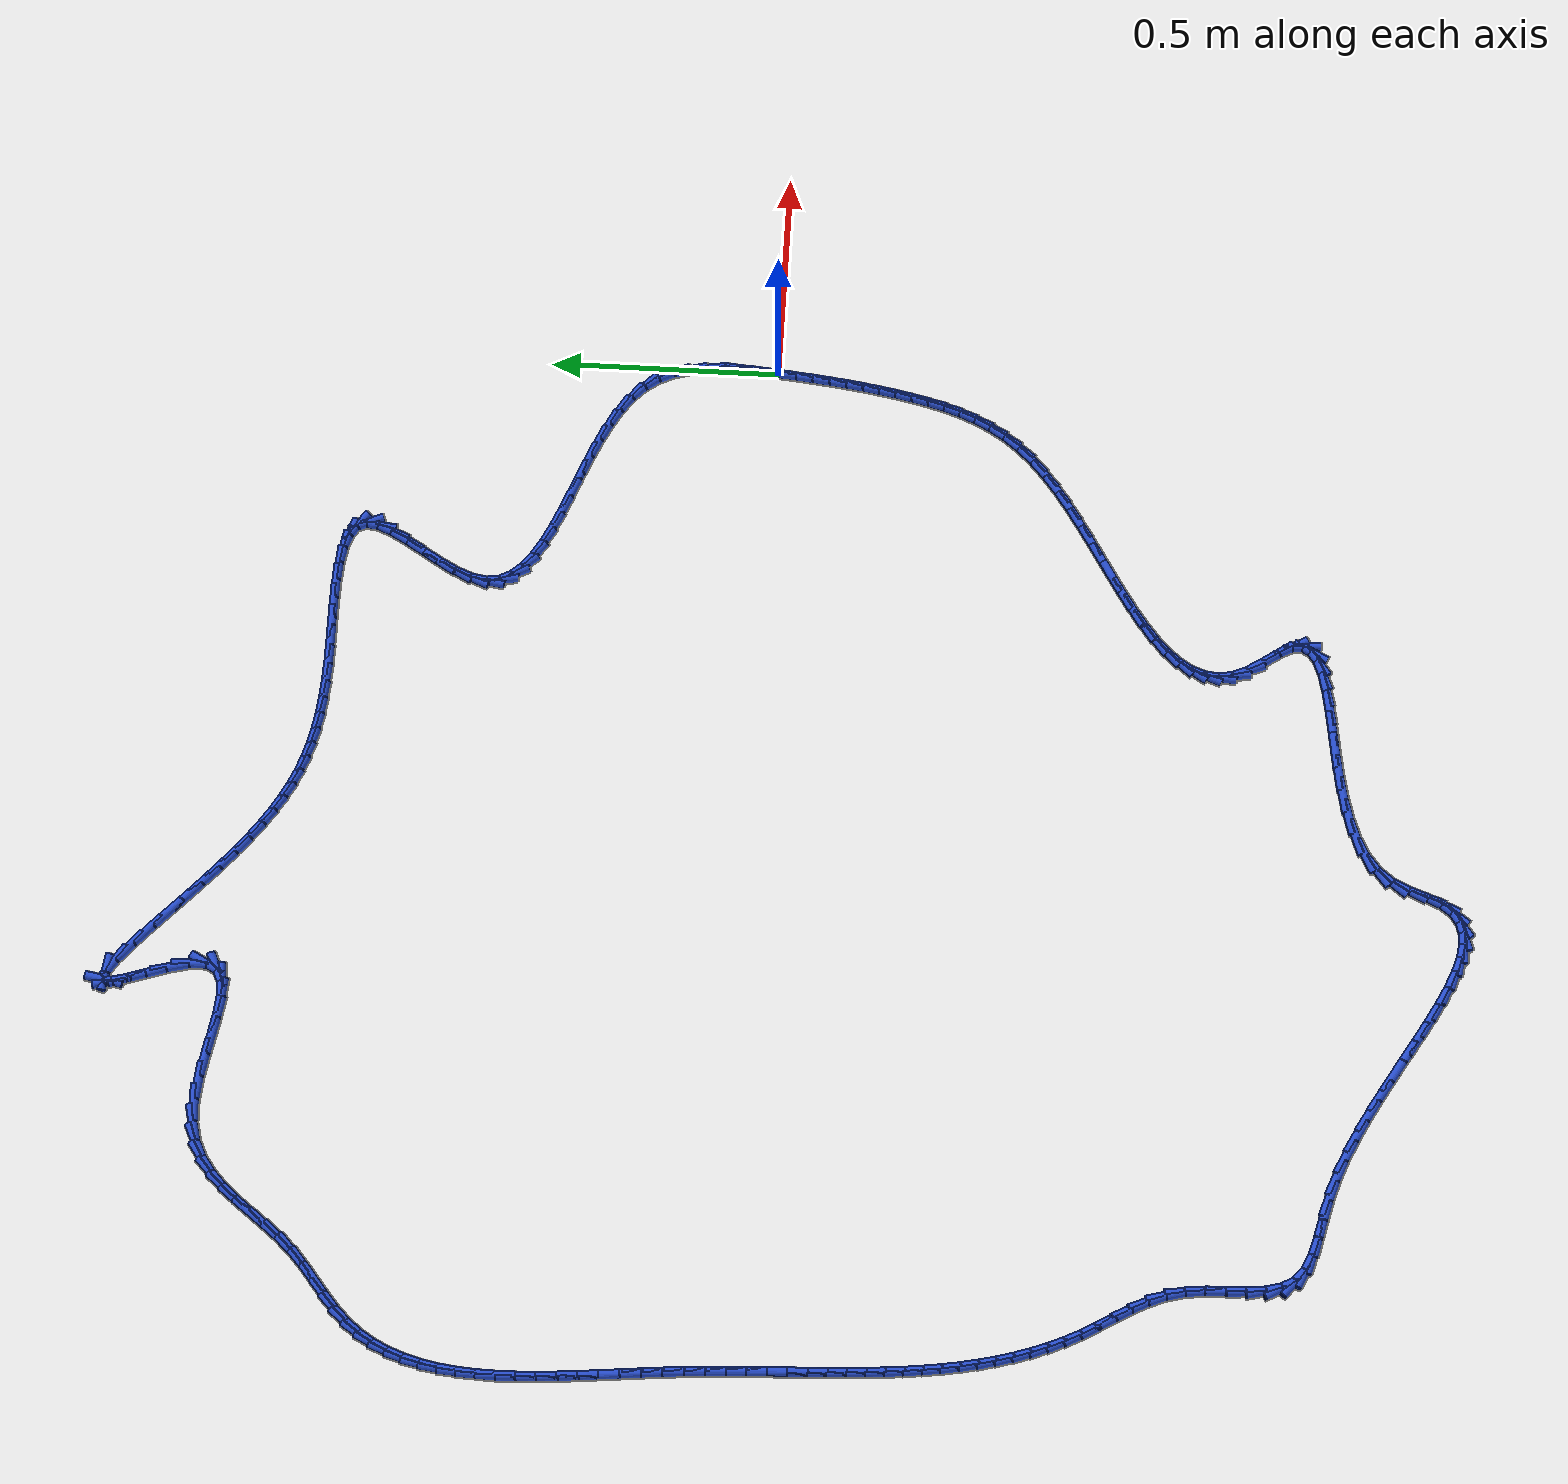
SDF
<sdf version="1.6">
 <world name="default">
  <light name="sun" type="directional">
   <pose>0 0 10 0 -0 0</pose>
   <diffuse>0.8 0.8 0.8 1</diffuse>
   <specular>0.2 0.2 0.2 1</specular>
   <attenuation>
    <range>1000</range>
    <constant>0.9</constant>
    <linear>0.01</linear>
    <quadratic>0.001</quadratic>
   </attenuation>
   <direction>-0.5 0.1 -0.9</direction>
  </light>
  <model name="ground_plane">
   <static>1</static>
   <link name="link">
    <collision name="collision">
     <geometry><plane><normal>0 0 1</normal><size>100 100</size></plane></geometry>
     <surface><friction><ode><mu>100</mu><mu2>50</mu2></ode></friction></surface>
    </collision>
    <visual name="visual">
     <cast_shadows>0</cast_shadows>
     <geometry><plane><normal>0 0 1</normal><size>100 100</size></plane></geometry>
     <material>
      <script><uri>file://media/materials/scripts/gazebo.material</uri><name>Gazebo/WhiteGlow</name></script>
     </material>
    </visual>
   </link>
  </model>
  <gravity>0 0 -9.8</gravity>
  <magnetic_field>6e-06 2.3e-05 -4.2e-05</magnetic_field>
  <atmosphere type="adiabatic"/>
  <physics name="default_physics" default="0" type="ode">
   <max_step_size>0.001</max_step_size>
   <real_time_factor>1</real_time_factor>
   <real_time_update_rate>1000</real_time_update_rate>
  </physics>
  <scene><ambient>0.4 0.4 0.4 1</ambient><background>0.7 0.7 0.7 1</background><shadows>1</shadows></scene>
  <spherical_coordinates>
   <surface_model>EARTH_WGS84</surface_model>
   <latitude_deg>0</latitude_deg>
   <longitude_deg>0</longitude_deg>
   <elevation>0</elevation>
   <heading_deg>0</heading_deg>
  </spherical_coordinates>
  <model name="line">
   <link name="link_0">
    <pose>2.3418766925686896e-17 0.0 0.01 0 1.57 1.48301899959872</pose>
    <collision name="collision">
     <geometry><cylinder><radius>0.01</radius><length>0.08</length></cylinder></geometry>
    </collision>
    <visual name="visual">
     <material>
      <script><name>Gazebo/Blue</name><uri>file://media/materials/scripts/gazebo.material</uri></script>
     </material>
     <geometry><cylinder><radius>0.01</radius><length>0.08</length></cylinder></geometry>
    </visual>
   </link>
   <link name="link_1">
    <pose>0.0034949813041329756 0.0397141344870754 0.01 0 1.57 1.5102847240519472</pose>
    <collision name="collision">
     <geometry><cylinder><radius>0.01</radius><length>0.08</length></cylinder></geometry>
    </collision>
    <visual name="visual">
     <material>
      <script><name>Gazebo/Blue</name><uri>file://media/materials/scripts/gazebo.material</uri></script>
     </material>
     <geometry><cylinder><radius>0.01</radius><length>0.08</length></cylinder></geometry>
    </visual>
   </link>
   <link name="link_2">
    <pose>0.0059192756810025615 0.07972852129482713 0.01 0 1.57 1.5585514268661935</pose>
    <collision name="collision">
     <geometry><cylinder><radius>0.01</radius><length>0.08</length></cylinder></geometry>
    </collision>
    <visual name="visual">
     <material>
      <script><name>Gazebo/Blue</name><uri>file://media/materials/scripts/gazebo.material</uri></script>
     </material>
     <geometry><cylinder><radius>0.01</radius><length>0.08</length></cylinder></geometry>
    </visual>
   </link>
   <link name="link_3">
    <pose>0.0064058495325591625 0.11946339341128547 0.01 0 1.57 -1.5112361139940027</pose>
    <collision name="collision">
     <geometry><cylinder><radius>0.01</radius><length>0.08</length></cylinder></geometry>
    </collision>
    <visual name="visual">
     <material>
      <script><name>Gazebo/Blue</name><uri>file://media/materials/scripts/gazebo.material</uri></script>
     </material>
     <geometry><cylinder><radius>0.01</radius><length>0.08</length></cylinder></geometry>
    </visual>
   </link>
   <link name="link_4">
    <pose>0.004087669260753157 0.1583389838244806 0.01 0 1.57 -1.4121379047766238</pose>
    <collision name="collision">
     <geometry><cylinder><radius>0.01</radius><length>0.08</length></cylinder></geometry>
    </collision>
    <visual name="visual">
     <material>
      <script><name>Gazebo/Blue</name><uri>file://media/materials/scripts/gazebo.material</uri></script>
     </material>
     <geometry><cylinder><radius>0.01</radius><length>0.08</length></cylinder></geometry>
    </visual>
   </link>
   <link name="link_5">
    <pose>-0.0019022987324650836 0.1957755255224428 0.01 0 1.57 -1.281841797179875</pose>
    <collision name="collision">
     <geometry><cylinder><radius>0.01</radius><length>0.08</length></cylinder></geometry>
    </collision>
    <visual name="visual">
     <material>
      <script><name>Gazebo/Blue</name><uri>file://media/materials/scripts/gazebo.material</uri></script>
     </material>
     <geometry><cylinder><radius>0.01</radius><length>0.08</length></cylinder></geometry>
    </visual>
   </link>
   <link name="link_6">
    <pose>-0.012431088045145165 0.23119325149320227 0.01 0 1.57 -1.1187924314241444</pose>
    <collision name="collision">
     <geometry><cylinder><radius>0.01</radius><length>0.08</length></cylinder></geometry>
    </collision>
    <visual name="visual">
     <material>
      <script><name>Gazebo/Blue</name><uri>file://media/materials/scripts/gazebo.material</uri></script>
     </material>
     <geometry><cylinder><radius>0.01</radius><length>0.08</length></cylinder></geometry>
    </visual>
   </link>
   <link name="link_7">
    <pose>-0.028365732275336713 0.2640123947247892 0.01 0 1.57 -0.9285013209521069</pose>
    <collision name="collision">
     <geometry><cylinder><radius>0.01</radius><length>0.08</length></cylinder></geometry>
    </collision>
    <visual name="visual">
     <material>
      <script><name>Gazebo/Blue</name><uri>file://media/materials/scripts/gazebo.material</uri></script>
     </material>
     <geometry><cylinder><radius>0.01</radius><length>0.08</length></cylinder></geometry>
    </visual>
   </link>
   <link name="link_8">
    <pose>-0.05054990800049826 0.2936657387752331 0.01 0 1.57 -0.7473281466656418</pose>
    <collision name="collision">
     <geometry><cylinder><radius>0.01</radius><length>0.08</length></cylinder></geometry>
    </collision>
    <visual name="visual">
     <material>
      <script><name>Gazebo/Blue</name><uri>file://media/materials/scripts/gazebo.material</uri></script>
     </material>
     <geometry><cylinder><radius>0.01</radius><length>0.08</length></cylinder></geometry>
    </visual>
   </link>
   <link name="link_9">
    <pose>-0.07900170106019329 0.320029686897392 0.01 0 1.57 -0.6088433574216038</pose>
    <collision name="collision">
     <geometry><cylinder><radius>0.01</radius><length>0.08</length></cylinder></geometry>
    </collision>
    <visual name="visual">
     <material>
      <script><name>Gazebo/Blue</name><uri>file://media/materials/scripts/gazebo.material</uri></script>
     </material>
     <geometry><cylinder><radius>0.01</radius><length>0.08</length></cylinder></geometry>
    </visual>
   </link>
   <link name="link_10">
    <pose>-0.11271210713015256 0.34353253495159436 0.01 0 1.57 -0.5081338897813198</pose>
    <collision name="collision">
     <geometry><cylinder><radius>0.01</radius><length>0.08</length></cylinder></geometry>
    </collision>
    <visual name="visual">
     <material>
      <script><name>Gazebo/Blue</name><uri>file://media/materials/scripts/gazebo.material</uri></script>
     </material>
     <geometry><cylinder><radius>0.01</radius><length>0.08</length></cylinder></geometry>
    </visual>
   </link>
   <link name="link_11">
    <pose>-0.15060786151989597 0.3646371082117627 0.01 0 1.57 -0.43727041215176216</pose>
    <collision name="collision">
     <geometry><cylinder><radius>0.01</radius><length>0.08</length></cylinder></geometry>
    </collision>
    <visual name="visual">
     <material>
      <script><name>Gazebo/Blue</name><uri>file://media/materials/scripts/gazebo.material</uri></script>
     </material>
     <geometry><cylinder><radius>0.01</radius><length>0.08</length></cylinder></geometry>
    </visual>
   </link>
   <link name="link_12">
    <pose>-0.19161569953894356 0.3838062319518194 0.01 0 1.57 -0.3900389414905041</pose>
    <collision name="collision">
     <geometry><cylinder><radius>0.01</radius><length>0.08</length></cylinder></geometry>
    </collision>
    <visual name="visual">
     <material>
      <script><name>Gazebo/Blue</name><uri>file://media/materials/scripts/gazebo.material</uri></script>
     </material>
     <geometry><cylinder><radius>0.01</radius><length>0.08</length></cylinder></geometry>
    </visual>
   </link>
   <link name="link_13">
    <pose>-0.2346623564968151 0.401502731445687 0.01 0 1.57 -0.36239353724382734</pose>
    <collision name="collision">
     <geometry><cylinder><radius>0.01</radius><length>0.08</length></cylinder></geometry>
    </collision>
    <visual name="visual">
     <material>
      <script><name>Gazebo/Blue</name><uri>file://media/materials/scripts/gazebo.material</uri></script>
     </material>
     <geometry><cylinder><radius>0.01</radius><length>0.08</length></cylinder></geometry>
    </visual>
   </link>
   <link name="link_14">
    <pose>-0.2786745677030307 0.41818943196728786 0.01 0 1.57 -0.35227594357470493</pose>
    <collision name="collision">
     <geometry><cylinder><radius>0.01</radius><length>0.08</length></cylinder></geometry>
    </collision>
    <visual name="visual">
     <material>
      <script><name>Gazebo/Blue</name><uri>file://media/materials/scripts/gazebo.material</uri></script>
     </material>
     <geometry><cylinder><radius>0.01</radius><length>0.08</length></cylinder></geometry>
    </visual>
   </link>
   <link name="link_15">
    <pose>-0.32257906846711026 0.4343291587905444 0.01 0 1.57 -0.3594734444192918</pose>
    <collision name="collision">
     <geometry><cylinder><radius>0.01</radius><length>0.08</length></cylinder></geometry>
    </collision>
    <visual name="visual">
     <material>
      <script><name>Gazebo/Blue</name><uri>file://media/materials/scripts/gazebo.material</uri></script>
     </material>
     <geometry><cylinder><radius>0.01</radius><length>0.08</length></cylinder></geometry>
    </visual>
   </link>
   <link name="link_16">
    <pose>-0.36530259409857374 0.4503847371893793 0.01 0 1.57 -0.3857470873406848</pose>
    <collision name="collision">
     <geometry><cylinder><radius>0.01</radius><length>0.08</length></cylinder></geometry>
    </collision>
    <visual name="visual">
     <material>
      <script><name>Gazebo/Blue</name><uri>file://media/materials/scripts/gazebo.material</uri></script>
     </material>
     <geometry><cylinder><radius>0.01</radius><length>0.08</length></cylinder></geometry>
    </visual>
   </link>
   <link name="link_17">
    <pose>-0.40577187990694114 0.4668189924377148 0.01 0 1.57 -0.43536456978689764</pose>
    <collision name="collision">
     <geometry><cylinder><radius>0.01</radius><length>0.08</length></cylinder></geometry>
    </collision>
    <visual name="visual">
     <material>
      <script><name>Gazebo/Blue</name><uri>file://media/materials/scripts/gazebo.material</uri></script>
     </material>
     <geometry><cylinder><radius>0.01</radius><length>0.08</length></cylinder></geometry>
    </visual>
   </link>
   <link name="link_18">
    <pose>-0.4429136612017323 0.4840947498094735 0.01 0 1.57 -0.5161694084390565</pose>
    <collision name="collision">
     <geometry><cylinder><radius>0.01</radius><length>0.08</length></cylinder></geometry>
    </collision>
    <visual name="visual">
     <material>
      <script><name>Gazebo/Blue</name><uri>file://media/materials/scripts/gazebo.material</uri></script>
     </material>
     <geometry><cylinder><radius>0.01</radius><length>0.08</length></cylinder></geometry>
    </visual>
   </link>
   <link name="link_19">
    <pose>-0.4756546732924673 0.5026748345785776 0.01 0 1.57 -0.6410792351259087</pose>
    <collision name="collision">
     <geometry><cylinder><radius>0.01</radius><length>0.08</length></cylinder></geometry>
    </collision>
    <visual name="visual">
     <material>
      <script><name>Gazebo/Blue</name><uri>file://media/materials/scripts/gazebo.material</uri></script>
     </material>
     <geometry><cylinder><radius>0.01</radius><length>0.08</length></cylinder></geometry>
    </visual>
   </link>
   <link name="link_20">
    <pose>-0.5029216514886659 0.5230220720189499 0.01 0 1.57 -0.8282741564114585</pose>
    <collision name="collision">
     <geometry><cylinder><radius>0.01</radius><length>0.08</length></cylinder></geometry>
    </collision>
    <visual name="visual">
     <material>
      <script><name>Gazebo/Blue</name><uri>file://media/materials/scripts/gazebo.material</uri></script>
     </material>
     <geometry><cylinder><radius>0.01</radius><length>0.08</length></cylinder></geometry>
    </visual>
   </link>
   <link name="link_21">
    <pose>-0.5236413310998482 0.5455992874045125 0.01 0 1.57 -1.092564170374915</pose>
    <collision name="collision">
     <geometry><cylinder><radius>0.01</radius><length>0.08</length></cylinder></geometry>
    </collision>
    <visual name="visual">
     <material>
      <script><name>Gazebo/Blue</name><uri>file://media/materials/scripts/gazebo.material</uri></script>
     </material>
     <geometry><cylinder><radius>0.01</radius><length>0.08</length></cylinder></geometry>
    </visual>
   </link>
   <link name="link_22">
    <pose>-0.5367404474355342 0.5708693060091881 0.01 0 1.57 -1.4170436256660386</pose>
    <collision name="collision">
     <geometry><cylinder><radius>0.01</radius><length>0.08</length></cylinder></geometry>
    </collision>
    <visual name="visual">
     <material>
      <script><name>Gazebo/Blue</name><uri>file://media/materials/scripts/gazebo.material</uri></script>
     </material>
     <geometry><cylinder><radius>0.01</radius><length>0.08</length></cylinder></geometry>
    </visual>
   </link>
   <link name="link_23">
    <pose>-0.5411457358052435 0.599294953106899 0.01 0 1.57 1.4061506158606747</pose>
    <collision name="collision">
     <geometry><cylinder><radius>0.01</radius><length>0.08</length></cylinder></geometry>
    </collision>
    <visual name="visual">
     <material>
      <script><name>Gazebo/Blue</name><uri>file://media/materials/scripts/gazebo.material</uri></script>
     </material>
     <geometry><cylinder><radius>0.01</radius><length>0.08</length></cylinder></geometry>
    </visual>
   </link>
   <link name="link_24">
    <pose>-0.5358245843745766 0.6313211867923071 0.01 0 1.57 1.1845515713231947</pose>
    <collision name="collision">
     <geometry><cylinder><radius>0.01</radius><length>0.08</length></cylinder></geometry>
    </collision>
    <visual name="visual">
     <material>
      <script><name>Gazebo/Blue</name><uri>file://media/materials/scripts/gazebo.material</uri></script>
     </material>
     <geometry><cylinder><radius>0.01</radius><length>0.08</length></cylinder></geometry>
    </visual>
   </link>
   <link name="link_25">
    <pose>-0.5214622480534541 0.6666379522033875 0.01 0 1.57 1.0700203127087764</pose>
    <collision name="collision">
     <geometry><cylinder><radius>0.01</radius><length>0.08</length></cylinder></geometry>
    </collision>
    <visual name="visual">
     <material>
      <script><name>Gazebo/Blue</name><uri>file://media/materials/scripts/gazebo.material</uri></script>
     </material>
     <geometry><cylinder><radius>0.01</radius><length>0.08</length></cylinder></geometry>
    </visual>
   </link>
   <link name="link_26">
    <pose>-0.5010585170572174 0.7039179420340143 0.01 0 1.57 1.0192693626224043</pose>
    <collision name="collision">
     <geometry><cylinder><radius>0.01</radius><length>0.08</length></cylinder></geometry>
    </collision>
    <visual name="visual">
     <material>
      <script><name>Gazebo/Blue</name><uri>file://media/materials/scripts/gazebo.material</uri></script>
     </material>
     <geometry><cylinder><radius>0.01</radius><length>0.08</length></cylinder></geometry>
    </visual>
   </link>
   <link name="link_27">
    <pose>-0.47777650290420265 0.7417620682649929 0.01 0 1.57 1.0147961115229551</pose>
    <collision name="collision">
     <geometry><cylinder><radius>0.01</radius><length>0.08</length></cylinder></geometry>
    </collision>
    <visual name="visual">
     <material>
      <script><name>Gazebo/Blue</name><uri>file://media/materials/scripts/gazebo.material</uri></script>
     </material>
     <geometry><cylinder><radius>0.01</radius><length>0.08</length></cylinder></geometry>
    </visual>
   </link>
   <link name="link_28">
    <pose>-0.4547793171127471 0.7787712428771287 0.01 0 1.57 1.058663958540398</pose>
    <collision name="collision">
     <geometry><cylinder><radius>0.01</radius><length>0.08</length></cylinder></geometry>
    </collision>
    <visual name="visual">
     <material>
      <script><name>Gazebo/Blue</name><uri>file://media/materials/scripts/gazebo.material</uri></script>
     </material>
     <geometry><cylinder><radius>0.01</radius><length>0.08</length></cylinder></geometry>
    </visual>
   </link>
   <link name="link_29">
    <pose>-0.4352300712011868 0.8135463778512266 0.01 0 1.57 1.1770355614612664</pose>
    <collision name="collision">
     <geometry><cylinder><radius>0.01</radius><length>0.08</length></cylinder></geometry>
    </collision>
    <visual name="visual">
     <material>
      <script><name>Gazebo/Blue</name><uri>file://media/materials/scripts/gazebo.material</uri></script>
     </material>
     <geometry><cylinder><radius>0.01</radius><length>0.08</length></cylinder></geometry>
    </visual>
   </link>
   <link name="link_30">
    <pose>-0.4222918766878586 0.844688385168092 0.01 0 1.57 1.450202538677667</pose>
    <collision name="collision">
     <geometry><cylinder><radius>0.01</radius><length>0.08</length></cylinder></geometry>
    </collision>
    <visual name="visual">
     <material>
      <script><name>Gazebo/Blue</name><uri>file://media/materials/scripts/gazebo.material</uri></script>
     </material>
     <geometry><cylinder><radius>0.01</radius><length>0.08</length></cylinder></geometry>
    </visual>
   </link>
   <link name="link_31">
    <pose>-0.41912784509109924 0.8707981768085302 0.01 0 1.57 -1.139373479864448</pose>
    <collision name="collision">
     <geometry><cylinder><radius>0.01</radius><length>0.08</length></cylinder></geometry>
    </collision>
    <visual name="visual">
     <material>
      <script><name>Gazebo/Blue</name><uri>file://media/materials/scripts/gazebo.material</uri></script>
     </material>
     <geometry><cylinder><radius>0.01</radius><length>0.08</length></cylinder></geometry>
    </visual>
   </link>
   <link name="link_32">
    <pose>-0.4283096279183051 0.8907436468919423 0.01 0 1.57 -0.5990839533540951</pose>
    <collision name="collision">
     <geometry><cylinder><radius>0.01</radius><length>0.08</length></cylinder></geometry>
    </collision>
    <visual name="visual">
     <material>
      <script><name>Gazebo/Blue</name><uri>file://media/materials/scripts/gazebo.material</uri></script>
     </material>
     <geometry><cylinder><radius>0.01</radius><length>0.08</length></cylinder></geometry>
    </visual>
   </link>
   <link name="link_33">
    <pose>-0.44905339026635877 0.9049073395924007 0.01 0 1.57 -0.2973705738031606</pose>
    <collision name="collision">
     <geometry><cylinder><radius>0.01</radius><length>0.08</length></cylinder></geometry>
    </collision>
    <visual name="visual">
     <material>
      <script><name>Gazebo/Blue</name><uri>file://media/materials/scripts/gazebo.material</uri></script>
     </material>
     <geometry><cylinder><radius>0.01</radius><length>0.08</length></cylinder></geometry>
    </visual>
   </link>
   <link name="link_34">
    <pose>-0.4793934488181903 0.9142052796426235 0.01 0 1.57 -0.13995081667476847</pose>
    <collision name="collision">
     <geometry><cylinder><radius>0.01</radius><length>0.08</length></cylinder></geometry>
    </collision>
    <visual name="visual">
     <material>
      <script><name>Gazebo/Blue</name><uri>file://media/materials/scripts/gazebo.material</uri></script>
     </material>
     <geometry><cylinder><radius>0.01</radius><length>0.08</length></cylinder></geometry>
    </visual>
   </link>
   <link name="link_35">
    <pose>-0.5173627994956134 0.9195540879603986 0.01 0 1.57 -0.05303777817666003</pose>
    <collision name="collision">
     <geometry><cylinder><radius>0.01</radius><length>0.08</length></cylinder></geometry>
    </collision>
    <visual name="visual">
     <material>
      <script><name>Gazebo/Blue</name><uri>file://media/materials/scripts/gazebo.material</uri></script>
     </material>
     <geometry><cylinder><radius>0.01</radius><length>0.08</length></cylinder></geometry>
    </visual>
   </link>
   <link name="link_36">
    <pose>-0.5609944382204414 0.9218703854635124 0.01 0 1.57 -0.004234511711053627</pose>
    <collision name="collision">
     <geometry><cylinder><radius>0.01</radius><length>0.08</length></cylinder></geometry>
    </collision>
    <visual name="visual">
     <material>
      <script><name>Gazebo/Blue</name><uri>file://media/materials/scripts/gazebo.material</uri></script>
     </material>
     <geometry><cylinder><radius>0.01</radius><length>0.08</length></cylinder></geometry>
    </visual>
   </link>
   <link name="link_37">
    <pose>-0.608321360914488 0.9220707930697521 0.01 0 1.57 0.020359173103185222</pose>
    <collision name="collision">
     <geometry><cylinder><radius>0.01</radius><length>0.08</length></cylinder></geometry>
    </collision>
    <visual name="visual">
     <material>
      <script><name>Gazebo/Blue</name><uri>file://media/materials/scripts/gazebo.material</uri></script>
     </material>
     <geometry><cylinder><radius>0.01</radius><length>0.08</length></cylinder></geometry>
    </visual>
   </link>
   <link name="link_38">
    <pose>-0.6573765634995669 0.9210719316969059 0.01 0 1.57 0.026245546910395066</pose>
    <collision name="collision">
     <geometry><cylinder><radius>0.01</radius><length>0.08</length></cylinder></geometry>
    </collision>
    <visual name="visual">
     <material>
      <script><name>Gazebo/Blue</name><uri>file://media/materials/scripts/gazebo.material</uri></script>
     </material>
     <geometry><cylinder><radius>0.01</radius><length>0.08</length></cylinder></geometry>
    </visual>
   </link>
   <link name="link_39">
    <pose>-0.7061930418974912 0.9197904222627599 0.01 0 1.57 0.014050279449397173</pose>
    <collision name="collision">
     <geometry><cylinder><radius>0.01</radius><length>0.08</length></cylinder></geometry>
    </collision>
    <visual name="visual">
     <material>
      <script><name>Gazebo/Blue</name><uri>file://media/materials/scripts/gazebo.material</uri></script>
     </material>
     <geometry><cylinder><radius>0.01</radius><length>0.08</length></cylinder></geometry>
    </visual>
   </link>
   <link name="link_40">
    <pose>-0.7528262154007621 0.9191351700250008 0.01 0 1.57 -0.012772914286360453</pose>
    <collision name="collision">
     <geometry><cylinder><radius>0.01</radius><length>0.08</length></cylinder></geometry>
    </collision>
    <visual name="visual">
     <material>
      <script><name>Gazebo/Blue</name><uri>file://media/materials/scripts/gazebo.material</uri></script>
     </material>
     <geometry><cylinder><radius>0.01</radius><length>0.08</length></cylinder></geometry>
    </visual>
   </link>
   <link name="link_41">
    <pose>-0.7962757413168073 0.9196901772782899 0.01 0 1.57 -0.047137525106969745</pose>
    <collision name="collision">
     <geometry><cylinder><radius>0.01</radius><length>0.08</length></cylinder></geometry>
    </collision>
    <visual name="visual">
     <material>
      <script><name>Gazebo/Blue</name><uri>file://media/materials/scripts/gazebo.material</uri></script>
     </material>
     <geometry><cylinder><radius>0.01</radius><length>0.08</length></cylinder></geometry>
    </visual>
   </link>
   <link name="link_42">
    <pose>-0.8368115665795276 0.9216023522191709 0.01 0 1.57 -0.08889991266092817</pose>
    <collision name="collision">
     <geometry><cylinder><radius>0.01</radius><length>0.08</length></cylinder></geometry>
    </collision>
    <visual name="visual">
     <material>
      <script><name>Gazebo/Blue</name><uri>file://media/materials/scripts/gazebo.material</uri></script>
     </material>
     <geometry><cylinder><radius>0.01</radius><length>0.08</length></cylinder></geometry>
    </visual>
   </link>
   <link name="link_43">
    <pose>-0.8747930757015474 0.9249878284578296 0.01 0 1.57 -0.13813084462011865</pose>
    <collision name="collision">
     <geometry><cylinder><radius>0.01</radius><length>0.08</length></cylinder></geometry>
    </collision>
    <visual name="visual">
     <material>
      <script><name>Gazebo/Blue</name><uri>file://media/materials/scripts/gazebo.material</uri></script>
     </material>
     <geometry><cylinder><radius>0.01</radius><length>0.08</length></cylinder></geometry>
    </visual>
   </link>
   <link name="link_44">
    <pose>-0.9105796531954921 0.9299627396044517 0.01 0 1.57 -0.19428603893547208</pose>
    <collision name="collision">
     <geometry><cylinder><radius>0.01</radius><length>0.08</length></cylinder></geometry>
    </collision>
    <visual name="visual">
     <material>
      <script><name>Gazebo/Blue</name><uri>file://media/materials/scripts/gazebo.material</uri></script>
     </material>
     <geometry><cylinder><radius>0.01</radius><length>0.08</length></cylinder></geometry>
    </visual>
   </link>
   <link name="link_45">
    <pose>-0.9445306835739862 0.9366432192692229 0.01 0 1.57 -0.2560608761660366</pose>
    <collision name="collision">
     <geometry><cylinder><radius>0.01</radius><length>0.08</length></cylinder></geometry>
    </collision>
    <visual name="visual">
     <material>
      <script><name>Gazebo/Blue</name><uri>file://media/materials/scripts/gazebo.material</uri></script>
     </material>
     <geometry><cylinder><radius>0.01</radius><length>0.08</length></cylinder></geometry>
    </visual>
   </link>
   <link name="link_46">
    <pose>-0.9770055513496545 0.9451454010623285 0.01 0 1.57 -0.3213866128710143</pose>
    <collision name="collision">
     <geometry><cylinder><radius>0.01</radius><length>0.08</length></cylinder></geometry>
    </collision>
    <visual name="visual">
     <material>
      <script><name>Gazebo/Blue</name><uri>file://media/materials/scripts/gazebo.material</uri></script>
     </material>
     <geometry><cylinder><radius>0.01</radius><length>0.08</length></cylinder></geometry>
    </visual>
   </link>
   <link name="link_47">
    <pose>-1.0083636410351224 0.9555854185939544 0.01 0 1.57 -0.387633240103913</pose>
    <collision name="collision">
     <geometry><cylinder><radius>0.01</radius><length>0.08</length></cylinder></geometry>
    </collision>
    <visual name="visual">
     <material>
      <script><name>Gazebo/Blue</name><uri>file://media/materials/scripts/gazebo.material</uri></script>
     </material>
     <geometry><cylinder><radius>0.01</radius><length>0.08</length></cylinder></geometry>
    </visual>
   </link>
   <link name="link_48">
    <pose>-1.0389643371430144 0.9680794054742863 0.01 0 1.57 -0.4519988271493742</pose>
    <collision name="collision">
     <geometry><cylinder><radius>0.01</radius><length>0.08</length></cylinder></geometry>
    </collision>
    <visual name="visual">
     <material>
      <script><name>Gazebo/Blue</name><uri>file://media/materials/scripts/gazebo.material</uri></script>
     </material>
     <geometry><cylinder><radius>0.01</radius><length>0.08</length></cylinder></geometry>
    </visual>
   </link>
   <link name="link_49">
    <pose>-1.0691670241859557 0.9827434953135099 0.01 0 1.57 -0.5119622731397211</pose>
    <collision name="collision">
     <geometry><cylinder><radius>0.01</radius><length>0.08</length></cylinder></geometry>
    </collision>
    <visual name="visual">
     <material>
      <script><name>Gazebo/Blue</name><uri>file://media/materials/scripts/gazebo.material</uri></script>
     </material>
     <geometry><cylinder><radius>0.01</radius><length>0.08</length></cylinder></geometry>
    </visual>
   </link>
   <link name="link_50">
    <pose>-1.099331086676571 0.9996938217218105 0.01 0 1.57 -0.5656372625766881</pose>
    <collision name="collision">
     <geometry><cylinder><radius>0.01</radius><length>0.08</length></cylinder></geometry>
    </collision>
    <visual name="visual">
     <material>
      <script><name>Gazebo/Blue</name><uri>file://media/materials/scripts/gazebo.material</uri></script>
     </material>
     <geometry><cylinder><radius>0.01</radius><length>0.08</length></cylinder></geometry>
    </visual>
   </link>
   <link name="link_51">
    <pose>-1.1298159091274855 1.0190465183093742 0.01 0 1.57 -0.6119249689035744</pose>
    <collision name="collision">
     <geometry><cylinder><radius>0.01</radius><length>0.08</length></cylinder></geometry>
    </collision>
    <visual name="visual">
     <material>
      <script><name>Gazebo/Blue</name><uri>file://media/materials/scripts/gazebo.material</uri></script>
     </material>
     <geometry><cylinder><radius>0.01</radius><length>0.08</length></cylinder></geometry>
    </visual>
   </link>
   <link name="link_52">
    <pose>-1.160980876051324 1.0409177186863865 0.01 0 1.57 -0.6504689448025031</pose>
    <collision name="collision">
     <geometry><cylinder><radius>0.01</radius><length>0.08</length></cylinder></geometry>
    </collision>
    <visual name="visual">
     <material>
      <script><name>Gazebo/Blue</name><uri>file://media/materials/scripts/gazebo.material</uri></script>
     </material>
     <geometry><cylinder><radius>0.01</radius><length>0.08</length></cylinder></geometry>
    </visual>
   </link>
   <link name="link_53">
    <pose>-1.193185371960711 1.0654235564630326 0.01 0 1.57 -0.6814885398059458</pose>
    <collision name="collision">
     <geometry><cylinder><radius>0.01</radius><length>0.08</length></cylinder></geometry>
    </collision>
    <visual name="visual">
     <material>
      <script><name>Gazebo/Blue</name><uri>file://media/materials/scripts/gazebo.material</uri></script>
     </material>
     <geometry><cylinder><radius>0.01</radius><length>0.08</length></cylinder></geometry>
    </visual>
   </link>
   <link name="link_54">
    <pose>-1.2267887813682719 1.0926801652494988 0.01 0 1.57 -0.705577640714517</pose>
    <collision name="collision">
     <geometry><cylinder><radius>0.01</radius><length>0.08</length></cylinder></geometry>
    </collision>
    <visual name="visual">
     <material>
      <script><name>Gazebo/Blue</name><uri>file://media/materials/scripts/gazebo.material</uri></script>
     </material>
     <geometry><cylinder><radius>0.01</radius><length>0.08</length></cylinder></geometry>
    </visual>
   </link>
   <link name="link_55">
    <pose>-1.262150488786631 1.12280367865597 0.01 0 1.57 -0.7235266784572728</pose>
    <collision name="collision">
     <geometry><cylinder><radius>0.01</radius><length>0.08</length></cylinder></geometry>
    </collision>
    <visual name="visual">
     <material>
      <script><name>Gazebo/Blue</name><uri>file://media/materials/scripts/gazebo.material</uri></script>
     </material>
     <geometry><cylinder><radius>0.01</radius><length>0.08</length></cylinder></geometry>
    </visual>
   </link>
   <link name="link_56">
    <pose>-1.299629878728414 1.1559102302926327 0.01 0 1.57 -0.73524054251963</pose>
    <collision name="collision">
     <geometry><cylinder><radius>0.01</radius><length>0.08</length></cylinder></geometry>
    </collision>
    <visual name="visual">
     <material>
      <script><name>Gazebo/Blue</name><uri>file://media/materials/scripts/gazebo.material</uri></script>
     </material>
     <geometry><cylinder><radius>0.01</radius><length>0.08</length></cylinder></geometry>
    </visual>
   </link>
   <link name="link_57">
    <pose>-1.3393691816638427 1.1918504423703078 0.01 0 1.57 -0.7340832677108964</pose>
    <collision name="collision">
     <geometry><cylinder><radius>0.01</radius><length>0.08</length></cylinder></geometry>
    </collision>
    <visual name="visual">
     <material>
      <script><name>Gazebo/Blue</name><uri>file://media/materials/scripts/gazebo.material</uri></script>
     </material>
     <geometry><cylinder><radius>0.01</radius><length>0.08</length></cylinder></geometry>
    </visual>
   </link>
   <link name="link_58">
    <pose>-1.3796368060279225 1.2281838394751738 0.01 0 1.57 -0.7154269703714127</pose>
    <collision name="collision">
     <geometry><cylinder><radius>0.01</radius><length>0.08</length></cylinder></geometry>
    </collision>
    <visual name="visual">
     <material>
      <script><name>Gazebo/Blue</name><uri>file://media/materials/scripts/gazebo.material</uri></script>
     </material>
     <geometry><cylinder><radius>0.01</radius><length>0.08</length></cylinder></geometry>
    </visual>
   </link>
   <link name="link_59">
    <pose>-1.4177431746995484 1.261298629819285 0.01 0 1.57 -0.6687835529094174</pose>
    <collision name="collision">
     <geometry><cylinder><radius>0.01</radius><length>0.08</length></cylinder></geometry>
    </collision>
    <visual name="visual">
     <material>
      <script><name>Gazebo/Blue</name><uri>file://media/materials/scripts/gazebo.material</uri></script>
     </material>
     <geometry><cylinder><radius>0.01</radius><length>0.08</length></cylinder></geometry>
    </visual>
   </link>
   <link name="link_60">
    <pose>-1.4509909949962605 1.287573587899027 0.01 0 1.57 -0.5517524189292895</pose>
    <collision name="collision">
     <geometry><cylinder><radius>0.01</radius><length>0.08</length></cylinder></geometry>
    </collision>
    <visual name="visual">
     <material>
      <script><name>Gazebo/Blue</name><uri>file://media/materials/scripts/gazebo.material</uri></script>
     </material>
     <geometry><cylinder><radius>0.01</radius><length>0.08</length></cylinder></geometry>
    </visual>
   </link>
   <link name="link_61">
    <pose>-1.4766829742356031 1.3033874882107896 0.01 0 1.57 -0.11169295148060926</pose>
    <collision name="collision">
     <geometry><cylinder><radius>0.01</radius><length>0.08</length></cylinder></geometry>
    </collision>
    <visual name="visual">
     <material>
      <script><name>Gazebo/Blue</name><uri>file://media/materials/scripts/gazebo.material</uri></script>
     </material>
     <geometry><cylinder><radius>0.01</radius><length>0.08</length></cylinder></geometry>
    </visual>
   </link>
   <link name="link_62">
    <pose>-1.4921218197351163 1.305119105250959 0.01 0 1.57 1.3940644213895959</pose>
    <collision name="collision">
     <geometry><cylinder><radius>0.01</radius><length>0.08</length></cylinder></geometry>
    </collision>
    <visual name="visual">
     <material>
      <script><name>Gazebo/Blue</name><uri>file://media/materials/scripts/gazebo.material</uri></script>
     </material>
     <geometry><cylinder><radius>0.01</radius><length>0.08</length></cylinder></geometry>
    </visual>
   </link>
   <link name="link_63">
    <pose>-1.4949090119919577 1.2895129072455203 0.01 0 1.57 -1.3175466240135953</pose>
    <collision name="collision">
     <geometry><cylinder><radius>0.01</radius><length>0.08</length></cylinder></geometry>
    </collision>
    <visual name="visual">
     <material>
      <script><name>Gazebo/Blue</name><uri>file://media/materials/scripts/gazebo.material</uri></script>
     </material>
     <geometry><cylinder><radius>0.01</radius><length>0.08</length></cylinder></geometry>
    </visual>
   </link>
   <link name="link_64">
    <pose>-1.4868822742854615 1.2584984577643017 0.01 0 1.57 -1.2421992598436171</pose>
    <collision name="collision">
     <geometry><cylinder><radius>0.01</radius><length>0.08</length></cylinder></geometry>
    </collision>
    <visual name="visual">
     <material>
      <script><name>Gazebo/Blue</name><uri>file://media/materials/scripts/gazebo.material</uri></script>
     </material>
     <geometry><cylinder><radius>0.01</radius><length>0.08</length></cylinder></geometry>
    </visual>
   </link>
   <link name="link_65">
    <pose>-1.473024576947186 1.217855053899099 0.01 0 1.57 -1.2524839921926199</pose>
    <collision name="collision">
     <geometry><cylinder><radius>0.01</radius><length>0.08</length></cylinder></geometry>
    </collision>
    <visual name="visual">
     <material>
      <script><name>Gazebo/Blue</name><uri>file://media/materials/scripts/gazebo.material</uri></script>
     </material>
     <geometry><cylinder><radius>0.01</radius><length>0.08</length></cylinder></geometry>
    </visual>
   </link>
   <link name="link_66">
    <pose>-1.458393380849566 1.1734531680063263 0.01 0 1.57 -1.3308367046124268</pose>
    <collision name="collision">
     <geometry><cylinder><radius>0.01</radius><length>0.08</length></cylinder></geometry>
    </collision>
    <visual name="visual">
     <material>
      <script><name>Gazebo/Blue</name><uri>file://media/materials/scripts/gazebo.material</uri></script>
     </material>
     <geometry><cylinder><radius>0.01</radius><length>0.08</length></cylinder></geometry>
    </visual>
   </link>
   <link name="link_67">
    <pose>-1.4480461468650367 1.1311632724423997 0.01 0 1.57 -1.5414716506826103</pose>
    <collision name="collision">
     <geometry><cylinder><radius>0.01</radius><length>0.08</length></cylinder></geometry>
    </collision>
    <visual name="visual">
     <material>
      <script><name>Gazebo/Blue</name><uri>file://media/materials/scripts/gazebo.material</uri></script>
     </material>
     <geometry><cylinder><radius>0.01</radius><length>0.08</length></cylinder></geometry>
    </visual>
   </link>
   <link name="link_68">
    <pose>-1.4470397856577737 1.0968552133212364 0.01 0 1.57 1.0788783696815802</pose>
    <collision name="collision">
     <geometry><cylinder><radius>0.01</radius><length>0.08</length></cylinder></geometry>
    </collision>
    <visual name="visual">
     <material>
      <script><name>Gazebo/Blue</name><uri>file://media/materials/scripts/gazebo.material</uri></script>
     </material>
     <geometry><cylinder><radius>0.01</radius><length>0.08</length></cylinder></geometry>
    </visual>
   </link>
   <link name="link_69">
    <pose>-1.4589219355356933 1.0746809954239753 0.01 0 1.57 0.4496814450634575</pose>
    <collision name="collision">
     <geometry><cylinder><radius>0.01</radius><length>0.08</length></cylinder></geometry>
    </collision>
    <visual name="visual">
     <material>
      <script><name>Gazebo/Blue</name><uri>file://media/materials/scripts/gazebo.material</uri></script>
     </material>
     <geometry><cylinder><radius>0.01</radius><length>0.08</length></cylinder></geometry>
    </visual>
   </link>
   <link name="link_70">
    <pose>-1.4824404182138615 1.0633295119212058 0.01 0 1.57 0.08848971333045619</pose>
    <collision name="collision">
     <geometry><cylinder><radius>0.01</radius><length>0.08</length></cylinder></geometry>
    </collision>
    <visual name="visual">
     <material>
      <script><name>Gazebo/Blue</name><uri>file://media/materials/scripts/gazebo.material</uri></script>
     </material>
     <geometry><cylinder><radius>0.01</radius><length>0.08</length></cylinder></geometry>
    </visual>
   </link>
   <link name="link_71">
    <pose>-1.5153910452092794 1.0604060858374942 0.01 0 1.57 -0.07724925856744368</pose>
    <collision name="collision">
     <geometry><cylinder><radius>0.01</radius><length>0.08</length></cylinder></geometry>
    </collision>
    <visual name="visual">
     <material>
      <script><name>Gazebo/Blue</name><uri>file://media/materials/scripts/gazebo.material</uri></script>
     </material>
     <geometry><cylinder><radius>0.01</radius><length>0.08</length></cylinder></geometry>
    </visual>
   </link>
   <link name="link_72">
    <pose>-1.5555696280389488 1.063516040197406 0.01 0 1.57 -0.1482041327249778</pose>
    <collision name="collision">
     <geometry><cylinder><radius>0.01</radius><length>0.08</length></cylinder></geometry>
    </collision>
    <visual name="visual">
     <material>
      <script><name>Gazebo/Blue</name><uri>file://media/materials/scripts/gazebo.material</uri></script>
     </material>
     <geometry><cylinder><radius>0.01</radius><length>0.08</length></cylinder></geometry>
    </visual>
   </link>
   <link name="link_73">
    <pose>-1.600771978219871 1.0702646980255075 0.01 0 1.57 -0.16492639531164513</pose>
    <collision name="collision">
     <geometry><cylinder><radius>0.01</radius><length>0.08</length></cylinder></geometry>
    </collision>
    <visual name="visual">
     <material>
      <script><name>Gazebo/Blue</name><uri>file://media/materials/scripts/gazebo.material</uri></script>
     </material>
     <geometry><cylinder><radius>0.01</radius><length>0.08</length></cylinder></geometry>
    </visual>
   </link>
   <link name="link_74">
    <pose>-1.6487939072690494 1.078257382346365 0.01 0 1.57 -0.1397574794900413</pose>
    <collision name="collision">
     <geometry><cylinder><radius>0.01</radius><length>0.08</length></cylinder></geometry>
    </collision>
    <visual name="visual">
     <material>
      <script><name>Gazebo/Blue</name><uri>file://media/materials/scripts/gazebo.material</uri></script>
     </material>
     <geometry><cylinder><radius>0.01</radius><length>0.08</length></cylinder></geometry>
    </visual>
   </link>
   <link name="link_75">
    <pose>-1.697431226703484 1.0850994161845446 0.01 0 1.57 -0.06995600874429944</pose>
    <collision name="collision">
     <geometry><cylinder><radius>0.01</radius><length>0.08</length></cylinder></geometry>
    </collision>
    <visual name="visual">
     <material>
      <script><name>Gazebo/Blue</name><uri>file://media/materials/scripts/gazebo.material</uri></script>
     </material>
     <geometry><cylinder><radius>0.01</radius><length>0.08</length></cylinder></geometry>
    </visual>
   </link>
   <link name="link_76">
    <pose>-1.7444797480401786 1.088396122564613 0.01 0 1.57 0.060960981338641224</pose>
    <collision name="collision">
     <geometry><cylinder><radius>0.01</radius><length>0.08</length></cylinder></geometry>
    </collision>
    <visual name="visual">
     <material>
      <script><name>Gazebo/Blue</name><uri>file://media/materials/scripts/gazebo.material</uri></script>
     </material>
     <geometry><cylinder><radius>0.01</radius><length>0.08</length></cylinder></geometry>
    </visual>
   </link>
   <link name="link_77">
    <pose>-1.7877378441819778 1.085755795064381 0.01 0 1.57 0.2573866097531275</pose>
    <collision name="collision">
     <geometry><cylinder><radius>0.01</radius><length>0.08</length></cylinder></geometry>
    </collision>
    <visual name="visual">
     <material>
      <script><name>Gazebo/Blue</name><uri>file://media/materials/scripts/gazebo.material</uri></script>
     </material>
     <geometry><cylinder><radius>0.01</radius><length>0.08</length></cylinder></geometry>
    </visual>
   </link>
   <link name="link_78">
    <pose>-1.8258188793652366 1.0757319090098154 0.01 0 1.57 0.45929069451560806</pose>
    <collision name="collision">
     <geometry><cylinder><radius>0.01</radius><length>0.08</length></cylinder></geometry>
    </collision>
    <visual name="visual">
     <material>
      <script><name>Gazebo/Blue</name><uri>file://media/materials/scripts/gazebo.material</uri></script>
     </material>
     <geometry><cylinder><radius>0.01</radius><length>0.08</length></cylinder></geometry>
    </visual>
   </link>
   <link name="link_79">
    <pose>-1.8593108027349114 1.0591679537909169 0.01 0 1.57 0.6344700896552029</pose>
    <collision name="collision">
     <geometry><cylinder><radius>0.01</radius><length>0.08</length></cylinder></geometry>
    </collision>
    <visual name="visual">
     <material>
      <script><name>Gazebo/Blue</name><uri>file://media/materials/scripts/gazebo.material</uri></script>
     </material>
     <geometry><cylinder><radius>0.01</radius><length>0.08</length></cylinder></geometry>
    </visual>
   </link>
   <link name="link_80">
    <pose>-1.8890947590160045 1.0372474507704252 0.01 0 1.57 0.76912073857601</pose>
    <collision name="collision">
     <geometry><cylinder><radius>0.01</radius><length>0.08</length></cylinder></geometry>
    </collision>
    <visual name="visual">
     <material>
      <script><name>Gazebo/Blue</name><uri>file://media/materials/scripts/gazebo.material</uri></script>
     </material>
     <geometry><cylinder><radius>0.01</radius><length>0.08</length></cylinder></geometry>
    </visual>
   </link>
   <link name="link_81">
    <pose>-1.9160518929335189 1.0111539213110818 0.01 0 1.57 0.8605243986561665</pose>
    <collision name="collision">
     <geometry><cylinder><radius>0.01</radius><length>0.08</length></cylinder></geometry>
    </collision>
    <visual name="visual">
     <material>
      <script><name>Gazebo/Blue</name><uri>file://media/materials/scripts/gazebo.material</uri></script>
     </material>
     <geometry><cylinder><radius>0.01</radius><length>0.08</length></cylinder></geometry>
    </visual>
   </link>
   <link name="link_82">
    <pose>-1.9410633492124556 0.982070886775626 0.01 0 1.57 0.911325802203178</pose>
    <collision name="collision">
     <geometry><cylinder><radius>0.01</radius><length>0.08</length></cylinder></geometry>
    </collision>
    <visual name="visual">
     <material>
      <script><name>Gazebo/Blue</name><uri>file://media/materials/scripts/gazebo.material</uri></script>
     </material>
     <geometry><cylinder><radius>0.01</radius><length>0.08</length></cylinder></geometry>
    </visual>
   </link>
   <link name="link_83">
    <pose>-1.9650102725778178 0.9511818685267979 0.01 0 1.57 0.9246616573894268</pose>
    <collision name="collision">
     <geometry><cylinder><radius>0.01</radius><length>0.08</length></cylinder></geometry>
    </collision>
    <visual name="visual">
     <material>
      <script><name>Gazebo/Blue</name><uri>file://media/materials/scripts/gazebo.material</uri></script>
     </material>
     <geometry><cylinder><radius>0.01</radius><length>0.08</length></cylinder></geometry>
    </visual>
   </link>
   <link name="link_84">
    <pose>-1.9887738077546069 0.9196703879273389 0.01 0 1.57 0.9019747291918594</pose>
    <collision name="collision">
     <geometry><cylinder><radius>0.01</radius><length>0.08</length></cylinder></geometry>
    </collision>
    <visual name="visual">
     <material>
      <script><name>Gazebo/Blue</name><uri>file://media/materials/scripts/gazebo.material</uri></script>
     </material>
     <geometry><cylinder><radius>0.01</radius><length>0.08</length></cylinder></geometry>
    </visual>
   </link>
   <link name="link_85">
    <pose>-2.013235099467826 0.8887199663399885 0.01 0 1.57 0.8426364904255277</pose>
    <collision name="collision">
     <geometry><cylinder><radius>0.01</radius><length>0.08</length></cylinder></geometry>
    </collision>
    <visual name="visual">
     <material>
      <script><name>Gazebo/Blue</name><uri>file://media/materials/scripts/gazebo.material</uri></script>
     </material>
     <geometry><cylinder><radius>0.01</radius><length>0.08</length></cylinder></geometry>
    </visual>
   </link>
   <link name="link_86">
    <pose>-2.039275292335897 0.8595141250179382 0.01 0 1.57 0.7584265235971142</pose>
    <collision name="collision">
     <geometry><cylinder><radius>0.01</radius><length>0.08</length></cylinder></geometry>
    </collision>
    <visual name="visual">
     <material>
      <script><name>Gazebo/Blue</name><uri>file://media/materials/scripts/gazebo.material</uri></script>
     </material>
     <geometry><cylinder><radius>0.01</radius><length>0.08</length></cylinder></geometry>
    </visual>
   </link>
   <link name="link_87">
    <pose>-2.0674084401912998 0.8328590634506005 0.01 0 1.57 0.7019475900518956</pose>
    <collision name="collision">
     <geometry><cylinder><radius>0.01</radius><length>0.08</length></cylinder></geometry>
    </collision>
    <visual name="visual">
     <material>
      <script><name>Gazebo/Blue</name><uri>file://media/materials/scripts/gazebo.material</uri></script>
     </material>
     <geometry><cylinder><radius>0.01</radius><length>0.08</length></cylinder></geometry>
    </visual>
   </link>
   <link name="link_88">
    <pose>-2.0967093038848406 0.808081574432287 0.01 0 1.57 0.6868038566524443</pose>
    <collision name="collision">
     <geometry><cylinder><radius>0.01</radius><length>0.08</length></cylinder></geometry>
    </collision>
    <visual name="visual">
     <material>
      <script><name>Gazebo/Blue</name><uri>file://media/materials/scripts/gazebo.material</uri></script>
     </material>
     <geometry><cylinder><radius>0.01</radius><length>0.08</length></cylinder></geometry>
    </visual>
   </link>
   <link name="link_89">
    <pose>-2.1258999452478844 0.7841459218647457 0.01 0 1.57 0.7147900512202157</pose>
    <collision name="collision">
     <geometry><cylinder><radius>0.01</radius><length>0.08</length></cylinder></geometry>
    </collision>
    <visual name="visual">
     <material>
      <script><name>Gazebo/Blue</name><uri>file://media/materials/scripts/gazebo.material</uri></script>
     </material>
     <geometry><cylinder><radius>0.01</radius><length>0.08</length></cylinder></geometry>
    </visual>
   </link>
   <link name="link_90">
    <pose>-2.1537024261117983 0.760016369649727 0.01 0 1.57 0.7897743422973054</pose>
    <collision name="collision">
     <geometry><cylinder><radius>0.01</radius><length>0.08</length></cylinder></geometry>
    </collision>
    <visual name="visual">
     <material>
      <script><name>Gazebo/Blue</name><uri>file://media/materials/scripts/gazebo.material</uri></script>
     </material>
     <geometry><cylinder><radius>0.01</radius><length>0.08</length></cylinder></geometry>
    </visual>
   </link>
   <link name="link_91">
    <pose>-2.178839840054045 0.7346579756073861 0.01 0 1.57 0.9020785091487951</pose>
    <collision name="collision">
     <geometry><cylinder><radius>0.01</radius><length>0.08</length></cylinder></geometry>
    </collision>
    <visual name="visual">
     <material>
      <script><name>Gazebo/Blue</name><uri>file://media/materials/scripts/gazebo.material</uri></script>
     </material>
     <geometry><cylinder><radius>0.01</radius><length>0.08</length></cylinder></geometry>
    </visual>
   </link>
   <link name="link_92">
    <pose>-2.2004275358975875 0.7073376340861671 0.01 0 1.57 1.0159643591724252</pose>
    <collision name="collision">
     <geometry><cylinder><radius>0.01</radius><length>0.08</length></cylinder></geometry>
    </collision>
    <visual name="visual">
     <material>
      <script><name>Gazebo/Blue</name><uri>file://media/materials/scripts/gazebo.material</uri></script>
     </material>
     <geometry><cylinder><radius>0.01</radius><length>0.08</length></cylinder></geometry>
    </visual>
   </link>
   <link name="link_93">
    <pose>-2.2185622456288914 0.6780774040636286 0.01 0 1.57 1.1227601798773306</pose>
    <collision name="collision">
     <geometry><cylinder><radius>0.01</radius><length>0.08</length></cylinder></geometry>
    </collision>
    <visual name="visual">
     <material>
      <script><name>Gazebo/Blue</name><uri>file://media/materials/scripts/gazebo.material</uri></script>
     </material>
     <geometry><cylinder><radius>0.01</radius><length>0.08</length></cylinder></geometry>
    </visual>
   </link>
   <link name="link_94">
    <pose>-2.2334916811926613 0.6470155221005749 0.01 0 1.57 1.2200898423174822</pose>
    <collision name="collision">
     <geometry><cylinder><radius>0.01</radius><length>0.08</length></cylinder></geometry>
    </collision>
    <visual name="visual">
     <material>
      <script><name>Gazebo/Blue</name><uri>file://media/materials/scripts/gazebo.material</uri></script>
     </material>
     <geometry><cylinder><radius>0.01</radius><length>0.08</length></cylinder></geometry>
    </visual>
   </link>
   <link name="link_95">
    <pose>-2.245463554533607 0.614290224757809 0.01 0 1.57 1.30669281832825</pose>
    <collision name="collision">
     <geometry><cylinder><radius>0.01</radius><length>0.08</length></cylinder></geometry>
    </collision>
    <visual name="visual">
     <material>
      <script><name>Gazebo/Blue</name><uri>file://media/materials/scripts/gazebo.material</uri></script>
     </material>
     <geometry><cylinder><radius>0.01</radius><length>0.08</length></cylinder></geometry>
    </visual>
   </link>
   <link name="link_96">
    <pose>-2.254725577596434 0.5800397485961352 0.01 0 1.57 1.382255184666243</pose>
    <collision name="collision">
     <geometry><cylinder><radius>0.01</radius><length>0.08</length></cylinder></geometry>
    </collision>
    <visual name="visual">
     <material>
      <script><name>Gazebo/Blue</name><uri>file://media/materials/scripts/gazebo.material</uri></script>
     </material>
     <geometry><cylinder><radius>0.01</radius><length>0.08</length></cylinder></geometry>
    </visual>
   </link>
   <link name="link_97">
    <pose>-2.2615254623258494 0.5444023301763563 0.01 0 1.57 1.447116923242679</pose>
    <collision name="collision">
     <geometry><cylinder><radius>0.01</radius><length>0.08</length></cylinder></geometry>
    </collision>
    <visual name="visual">
     <material>
      <script><name>Gazebo/Blue</name><uri>file://media/materials/scripts/gazebo.material</uri></script>
     </material>
     <geometry><cylinder><radius>0.01</radius><length>0.08</length></cylinder></geometry>
    </visual>
   </link>
   <link name="link_98">
    <pose>-2.266110920666562 0.5075162060592759 0.01 0 1.57 1.501984649858105</pose>
    <collision name="collision">
     <geometry><cylinder><radius>0.01</radius><length>0.08</length></cylinder></geometry>
    </collision>
    <visual name="visual">
     <material>
      <script><name>Gazebo/Blue</name><uri>file://media/materials/scripts/gazebo.material</uri></script>
     </material>
     <geometry><cylinder><radius>0.01</radius><length>0.08</length></cylinder></geometry>
    </visual>
   </link>
   <link name="link_99">
    <pose>-2.268729664563278 0.46951961280569837 0.01 0 1.57 1.5477116803301874</pose>
    <collision name="collision">
     <geometry><cylinder><radius>0.01</radius><length>0.08</length></cylinder></geometry>
    </collision>
    <visual name="visual">
     <material>
      <script><name>Gazebo/Blue</name><uri>file://media/materials/scripts/gazebo.material</uri></script>
     </material>
     <geometry><cylinder><radius>0.01</radius><length>0.08</length></cylinder></geometry>
    </visual>
   </link>
   <link name="link_100">
    <pose>-2.2696294059607043 0.4305507869764263 0.01 0 1.57 -1.5564378001405421</pose>
    <collision name="collision">
     <geometry><cylinder><radius>0.01</radius><length>0.08</length></cylinder></geometry>
    </collision>
    <visual name="visual">
     <material>
      <script><name>Gazebo/Blue</name><uri>file://media/materials/scripts/gazebo.material</uri></script>
     </material>
     <geometry><cylinder><radius>0.01</radius><length>0.08</length></cylinder></geometry>
    </visual>
   </link>
   <link name="link_101">
    <pose>-2.26905785680355 0.39074796513226423 0.01 0 1.57 -1.526499627401595</pose>
    <collision name="collision">
     <geometry><cylinder><radius>0.01</radius><length>0.08</length></cylinder></geometry>
    </collision>
    <visual name="visual">
     <material>
      <script><name>Gazebo/Blue</name><uri>file://media/materials/scripts/gazebo.material</uri></script>
     </material>
     <geometry><cylinder><radius>0.01</radius><length>0.08</length></cylinder></geometry>
    </visual>
   </link>
   <link name="link_102">
    <pose>-2.2672627290365206 0.35024938383401494 0.01 0 1.57 -1.5034056576064672</pose>
    <collision name="collision">
     <geometry><cylinder><radius>0.01</radius><length>0.08</length></cylinder></geometry>
    </collision>
    <visual name="visual">
     <material>
      <script><name>Gazebo/Blue</name><uri>file://media/materials/scripts/gazebo.material</uri></script>
     </material>
     <geometry><cylinder><radius>0.01</radius><length>0.08</length></cylinder></geometry>
    </visual>
   </link>
   <link name="link_103">
    <pose>-2.264491734604323 0.3091932796424828 0.01 0 1.57 -1.4866287677100554</pose>
    <collision name="collision">
     <geometry><cylinder><radius>0.01</radius><length>0.08</length></cylinder></geometry>
    </collision>
    <visual name="visual">
     <material>
      <script><name>Gazebo/Blue</name><uri>file://media/materials/scripts/gazebo.material</uri></script>
     </material>
     <geometry><cylinder><radius>0.01</radius><length>0.08</length></cylinder></geometry>
    </visual>
   </link>
   <link name="link_104">
    <pose>-2.2609925854516666 0.2677178891184704 0.01 0 1.57 -1.4757784507355776</pose>
    <collision name="collision">
     <geometry><cylinder><radius>0.01</radius><length>0.08</length></cylinder></geometry>
    </collision>
    <visual name="visual">
     <material>
      <script><name>Gazebo/Blue</name><uri>file://media/materials/scripts/gazebo.material</uri></script>
     </material>
     <geometry><cylinder><radius>0.01</radius><length>0.08</length></cylinder></geometry>
    </visual>
   </link>
   <link name="link_105">
    <pose>-2.257012993523257 0.2259614488227824 0.01 0 1.57 -1.470598441089765</pose>
    <collision name="collision">
     <geometry><cylinder><radius>0.01</radius><length>0.08</length></cylinder></geometry>
    </collision>
    <visual name="visual">
     <material>
      <script><name>Gazebo/Blue</name><uri>file://media/materials/scripts/gazebo.material</uri></script>
     </material>
     <geometry><cylinder><radius>0.01</radius><length>0.08</length></cylinder></geometry>
    </visual>
   </link>
   <link name="link_106">
    <pose>-2.2528006707638024 0.18406219531622148 0.01 0 1.57 -1.4709632592744175</pose>
    <collision name="collision">
     <geometry><cylinder><radius>0.01</radius><length>0.08</length></cylinder></geometry>
    </collision>
    <visual name="visual">
     <material>
      <script><name>Gazebo/Blue</name><uri>file://media/materials/scripts/gazebo.material</uri></script>
     </material>
     <geometry><cylinder><radius>0.01</radius><length>0.08</length></cylinder></geometry>
    </visual>
   </link>
   <link name="link_107">
    <pose>-2.248603329118008 0.14215836515959196 0.01 0 1.57 -1.4768758923383496</pose>
    <collision name="collision">
     <geometry><cylinder><radius>0.01</radius><length>0.08</length></cylinder></geometry>
    </collision>
    <visual name="visual">
     <material>
      <script><name>Gazebo/Blue</name><uri>file://media/materials/scripts/gazebo.material</uri></script>
     </material>
     <geometry><cylinder><radius>0.01</radius><length>0.08</length></cylinder></geometry>
    </visual>
   </link>
   <link name="link_108">
    <pose>-2.2446686805305847 0.10038819491369659 0.01 0 1.57 -1.4883190256080854</pose>
    <collision name="collision">
     <geometry><cylinder><radius>0.01</radius><length>0.08</length></cylinder></geometry>
    </collision>
    <visual name="visual">
     <material>
      <script><name>Gazebo/Blue</name><uri>file://media/materials/scripts/gazebo.material</uri></script>
     </material>
     <geometry><cylinder><radius>0.01</radius><length>0.08</length></cylinder></geometry>
    </visual>
   </link>
   <link name="link_109">
    <pose>-2.2412380441411743 0.05888763856509549 0.01 0 1.57 -1.5015631289805005</pose>
    <collision name="collision">
     <geometry><cylinder><radius>0.01</radius><length>0.08</length></cylinder></geometry>
    </collision>
    <visual name="visual">
     <material>
      <script><name>Gazebo/Blue</name><uri>file://media/materials/scripts/gazebo.material</uri></script>
     </material>
     <geometry><cylinder><radius>0.01</radius><length>0.08</length></cylinder></geometry>
    </visual>
   </link>
   <link name="link_110">
    <pose>-2.2383841786601066 0.017732464987421113 0.01 0 1.57 -1.5123856461197271</pose>
    <collision name="collision">
     <geometry><cylinder><radius>0.01</radius><length>0.08</length></cylinder></geometry>
    </collision>
    <visual name="visual">
     <material>
      <script><name>Gazebo/Blue</name><uri>file://media/materials/scripts/gazebo.material</uri></script>
     </material>
     <geometry><cylinder><radius>0.01</radius><length>0.08</length></cylinder></geometry>
    </visual>
   </link>
   <link name="link_111">
    <pose>-2.2359983782185555 -0.023066349532141227 0.01 0 1.57 -1.5205003320529569</pose>
    <collision name="collision">
     <geometry><cylinder><radius>0.01</radius><length>0.08</length></cylinder></geometry>
    </collision>
    <visual name="visual">
     <material>
      <script><name>Gazebo/Blue</name><uri>file://media/materials/scripts/gazebo.material</uri></script>
     </material>
     <geometry><cylinder><radius>0.01</radius><length>0.08</length></cylinder></geometry>
    </visual>
   </link>
   <link name="link_112">
    <pose>-2.233962958909521 -0.06350103434751572 0.01 0 1.57 -1.5258292361275618</pose>
    <collision name="collision">
     <geometry><cylinder><radius>0.01</radius><length>0.08</length></cylinder></geometry>
    </collision>
    <visual name="visual">
     <material>
      <script><name>Gazebo/Blue</name><uri>file://media/materials/scripts/gazebo.material</uri></script>
     </material>
     <geometry><cylinder><radius>0.01</radius><length>0.08</length></cylinder></geometry>
    </visual>
   </link>
   <link name="link_113">
    <pose>-2.2321602368260023 -0.10356381881262608 0.01 0 1.57 -1.5282922952049893</pose>
    <collision name="collision">
     <geometry><cylinder><radius>0.01</radius><length>0.08</length></cylinder></geometry>
    </collision>
    <visual name="visual">
     <material>
      <script><name>Gazebo/Blue</name><uri>file://media/materials/scripts/gazebo.material</uri></script>
     </material>
     <geometry><cylinder><radius>0.01</radius><length>0.08</length></cylinder></geometry>
    </visual>
   </link>
   <link name="link_114">
    <pose>-2.2304725280609996 -0.14324693228139704 0.01 0 1.57 -1.527805896216756</pose>
    <collision name="collision">
     <geometry><cylinder><radius>0.01</radius><length>0.08</length></cylinder></geometry>
    </collision>
    <visual name="visual">
     <material>
      <script><name>Gazebo/Blue</name><uri>file://media/materials/scripts/gazebo.material</uri></script>
     </material>
     <geometry><cylinder><radius>0.01</radius><length>0.08</length></cylinder></geometry>
    </visual>
   </link>
   <link name="link_115">
    <pose>-2.228782148707513 -0.18254260410775044 0.01 0 1.57 -1.5242820235541341</pose>
    <collision name="collision">
     <geometry><cylinder><radius>0.01</radius><length>0.08</length></cylinder></geometry>
    </collision>
    <visual name="visual">
     <material>
      <script><name>Gazebo/Blue</name><uri>file://media/materials/scripts/gazebo.material</uri></script>
     </material>
     <geometry><cylinder><radius>0.01</radius><length>0.08</length></cylinder></geometry>
    </visual>
   </link>
   <link name="link_116">
    <pose>-2.2269714148585398 -0.22144306364561084 0.01 0 1.57 -1.5176281313855693</pose>
    <collision name="collision">
     <geometry><cylinder><radius>0.01</radius><length>0.08</length></cylinder></geometry>
    </collision>
    <visual name="visual">
     <material>
      <script><name>Gazebo/Blue</name><uri>file://media/materials/scripts/gazebo.material</uri></script>
     </material>
     <geometry><cylinder><radius>0.01</radius><length>0.08</length></cylinder></geometry>
    </visual>
   </link>
   <link name="link_117">
    <pose>-2.224922642607081 -0.2599405402489021 0.01 0 1.57 -1.5077479076148295</pose>
    <collision name="collision">
     <geometry><cylinder><radius>0.01</radius><length>0.08</length></cylinder></geometry>
    </collision>
    <visual name="visual">
     <material>
      <script><name>Gazebo/Blue</name><uri>file://media/materials/scripts/gazebo.material</uri></script>
     </material>
     <geometry><cylinder><radius>0.01</radius><length>0.08</length></cylinder></geometry>
    </visual>
   </link>
   <link name="link_118">
    <pose>-2.222518148046136 -0.2980272632715488 0.01 0 1.57 -1.4945431263242273</pose>
    <collision name="collision">
     <geometry><cylinder><radius>0.01</radius><length>0.08</length></cylinder></geometry>
    </collision>
    <visual name="visual">
     <material>
      <script><name>Gazebo/Blue</name><uri>file://media/materials/scripts/gazebo.material</uri></script>
     </material>
     <geometry><cylinder><radius>0.01</radius><length>0.08</length></cylinder></geometry>
    </visual>
   </link>
   <link name="link_119">
    <pose>-2.2196402472687042 -0.33569546206747297 0.01 0 1.57 -1.4779168122918045</pose>
    <collision name="collision">
     <geometry><cylinder><radius>0.01</radius><length>0.08</length></cylinder></geometry>
    </collision>
    <visual name="visual">
     <material>
      <script><name>Gazebo/Blue</name><uri>file://media/materials/scripts/gazebo.material</uri></script>
     </material>
     <geometry><cylinder><radius>0.01</radius><length>0.08</length></cylinder></geometry>
    </visual>
   </link>
   <link name="link_120">
    <pose>-2.2161712563677853 -0.3729373659905992 0.01 0 1.57 -1.457777953450756</pose>
    <collision name="collision">
     <geometry><cylinder><radius>0.01</radius><length>0.08</length></cylinder></geometry>
    </collision>
    <visual name="visual">
     <material>
      <script><name>Gazebo/Blue</name><uri>file://media/materials/scripts/gazebo.material</uri></script>
     </material>
     <geometry><cylinder><radius>0.01</radius><length>0.08</length></cylinder></geometry>
    </visual>
   </link>
   <link name="link_121">
    <pose>-2.2119934914363792 -0.40974520439485096 0.01 0 1.57 -1.4340479785679279</pose>
    <collision name="collision">
     <geometry><cylinder><radius>0.01</radius><length>0.08</length></cylinder></geometry>
    </collision>
    <visual name="visual">
     <material>
      <script><name>Gazebo/Blue</name><uri>file://media/materials/scripts/gazebo.material</uri></script>
     </material>
     <geometry><cylinder><radius>0.01</radius><length>0.08</length></cylinder></geometry>
    </visual>
   </link>
   <link name="link_122">
    <pose>-2.2069892685674852 -0.44611120663415343 0.01 0 1.57 -1.406669145890333</pose>
    <collision name="collision">
     <geometry><cylinder><radius>0.01</radius><length>0.08</length></cylinder></geometry>
    </collision>
    <visual name="visual">
     <material>
      <script><name>Gazebo/Blue</name><uri>file://media/materials/scripts/gazebo.material</uri></script>
     </material>
     <geometry><cylinder><radius>0.01</radius><length>0.08</length></cylinder></geometry>
    </visual>
   </link>
   <link name="link_123">
    <pose>-2.2010409038541026 -0.482027602062428 0.01 0 1.57 -1.3756148379651798</pose>
    <collision name="collision">
     <geometry><cylinder><radius>0.01</radius><length>0.08</length></cylinder></geometry>
    </collision>
    <visual name="visual">
     <material>
      <script><name>Gazebo/Blue</name><uri>file://media/materials/scripts/gazebo.material</uri></script>
     </material>
     <geometry><cylinder><radius>0.01</radius><length>0.08</length></cylinder></geometry>
    </visual>
   </link>
   <link name="link_124">
    <pose>-2.1940307133892314 -0.5174866200335997 0.01 0 1.57 -1.3409015036684935</pose>
    <collision name="collision">
     <geometry><cylinder><radius>0.01</radius><length>0.08</length></cylinder></geometry>
    </collision>
    <visual name="visual">
     <material>
      <script><name>Gazebo/Blue</name><uri>file://media/materials/scripts/gazebo.material</uri></script>
     </material>
     <geometry><cylinder><radius>0.01</radius><length>0.08</length></cylinder></geometry>
    </visual>
   </link>
   <link name="link_125">
    <pose>-2.1858410132658705 -0.5524804899015919 0.01 0 1.57 -1.302601618582218</pose>
    <collision name="collision">
     <geometry><cylinder><radius>0.01</radius><length>0.08</length></cylinder></geometry>
    </collision>
    <visual name="visual">
     <material>
      <script><name>Gazebo/Blue</name><uri>file://media/materials/scripts/gazebo.material</uri></script>
     </material>
     <geometry><cylinder><radius>0.01</radius><length>0.08</length></cylinder></geometry>
    </visual>
   </link>
   <link name="link_126">
    <pose>-2.1763541195770197 -0.5870014410203296 0.01 0 1.57 -1.2608565667151115</pose>
    <collision name="collision">
     <geometry><cylinder><radius>0.01</radius><length>0.08</length></cylinder></geometry>
    </collision>
    <visual name="visual">
     <material>
      <script><name>Gazebo/Blue</name><uri>file://media/materials/scripts/gazebo.material</uri></script>
     </material>
     <geometry><cylinder><radius>0.01</radius><length>0.08</length></cylinder></geometry>
    </visual>
   </link>
   <link name="link_127">
    <pose>-2.1654523484156787 -0.6210417027437344 0.01 0 1.57 -1.2158878469187202</pose>
    <collision name="collision">
     <geometry><cylinder><radius>0.01</radius><length>0.08</length></cylinder></geometry>
    </collision>
    <visual name="visual">
     <material>
      <script><name>Gazebo/Blue</name><uri>file://media/materials/scripts/gazebo.material</uri></script>
     </material>
     <geometry><cylinder><radius>0.01</radius><length>0.08</length></cylinder></geometry>
    </visual>
   </link>
   <link name="link_128">
    <pose>-2.153018015874847 -0.6545935044257313 0.01 0 1.57 -1.1680046048767039</pose>
    <collision name="collision">
     <geometry><cylinder><radius>0.01</radius><length>0.08</length></cylinder></geometry>
    </collision>
    <visual name="visual">
     <material>
      <script><name>Gazebo/Blue</name><uri>file://media/materials/scripts/gazebo.material</uri></script>
     </material>
     <geometry><cylinder><radius>0.01</radius><length>0.08</length></cylinder></geometry>
    </visual>
   </link>
   <link name="link_129">
    <pose>-2.1389334380475242 -0.6876490754202438 0.01 0 1.57 -1.1176053666232557</pose>
    <collision name="collision">
     <geometry><cylinder><radius>0.01</radius><length>0.08</length></cylinder></geometry>
    </collision>
    <visual name="visual">
     <material>
      <script><name>Gazebo/Blue</name><uri>file://media/materials/scripts/gazebo.material</uri></script>
     </material>
     <geometry><cylinder><radius>0.01</radius><length>0.08</length></cylinder></geometry>
    </visual>
   </link>
   <link name="link_130">
    <pose>-2.1230809310267102 -0.7202006450811956 0.01 0 1.57 -1.0659489934735233</pose>
    <collision name="collision">
     <geometry><cylinder><radius>0.01</radius><length>0.08</length></cylinder></geometry>
    </collision>
    <visual name="visual">
     <material>
      <script><name>Gazebo/Blue</name><uri>file://media/materials/scripts/gazebo.material</uri></script>
     </material>
     <geometry><cylinder><radius>0.01</radius><length>0.08</length></cylinder></geometry>
    </visual>
   </link>
   <link name="link_131">
    <pose>-2.105368966353822 -0.752251929706147 0.01 0 1.57 -1.033960128867715</pose>
    <collision name="collision">
     <geometry><cylinder><radius>0.01</radius><length>0.08</length></cylinder></geometry>
    </collision>
    <visual name="visual">
     <material>
      <script><name>Gazebo/Blue</name><uri>file://media/materials/scripts/gazebo.material</uri></script>
     </material>
     <geometry><cylinder><radius>0.01</radius><length>0.08</length></cylinder></geometry>
    </visual>
   </link>
   <link name="link_132">
    <pose>-2.086406496624533 -0.7841142826959975 0.01 0 1.57 -1.0429254036376472</pose>
    <collision name="collision">
     <geometry><cylinder><radius>0.01</radius><length>0.08</length></cylinder></geometry>
    </collision>
    <visual name="visual">
     <material>
      <script><name>Gazebo/Blue</name><uri>file://media/materials/scripts/gazebo.material</uri></script>
     </material>
     <geometry><cylinder><radius>0.01</radius><length>0.08</length></cylinder></geometry>
    </visual>
   </link>
   <link name="link_133">
    <pose>-2.067562752053534 -0.8164329559961276 0.01 0 1.57 -1.092916642152559</pose>
    <collision name="collision">
     <geometry><cylinder><radius>0.01</radius><length>0.08</length></cylinder></geometry>
    </collision>
    <visual name="visual">
     <material>
      <script><name>Gazebo/Blue</name><uri>file://media/materials/scripts/gazebo.material</uri></script>
     </material>
     <geometry><cylinder><radius>0.01</radius><length>0.08</length></cylinder></geometry>
    </visual>
   </link>
   <link name="link_134">
    <pose>-2.0502451027794244 -0.8498699518346579 0.01 0 1.57 -1.1830348076666632</pose>
    <collision name="collision">
     <geometry><cylinder><radius>0.01</radius><length>0.08</length></cylinder></geometry>
    </collision>
    <visual name="visual">
     <material>
      <script><name>Gazebo/Blue</name><uri>file://media/materials/scripts/gazebo.material</uri></script>
     </material>
     <geometry><cylinder><radius>0.01</radius><length>0.08</length></cylinder></geometry>
    </visual>
   </link>
   <link name="link_135">
    <pose>-2.0358609189408083 -0.8850872724397104 0.01 0 1.57 -1.3101699972998422</pose>
    <collision name="collision">
     <geometry><cylinder><radius>0.01</radius><length>0.08</length></cylinder></geometry>
    </collision>
    <visual name="visual">
     <material>
      <script><name>Gazebo/Blue</name><uri>file://media/materials/scripts/gazebo.material</uri></script>
     </material>
     <geometry><cylinder><radius>0.01</radius><length>0.08</length></cylinder></geometry>
    </visual>
   </link>
   <link name="link_136">
    <pose>-2.025817408601669 -0.9227468152250876 0.01 0 1.57 -1.445402480916084</pose>
    <collision name="collision">
     <geometry><cylinder><radius>0.01</radius><length>0.08</length></cylinder></geometry>
    </collision>
    <visual name="visual">
     <material>
      <script><name>Gazebo/Blue</name><uri>file://media/materials/scripts/gazebo.material</uri></script>
     </material>
     <geometry><cylinder><radius>0.01</radius><length>0.08</length></cylinder></geometry>
    </visual>
   </link>
   <link name="link_137">
    <pose>-2.0207424661245743 -0.9630064922559392 0.01 0 1.57 -1.5209872679867773</pose>
    <collision name="collision">
     <geometry><cylinder><radius>0.01</radius><length>0.08</length></cylinder></geometry>
    </collision>
    <visual name="visual">
     <material>
      <script><name>Gazebo/Blue</name><uri>file://media/materials/scripts/gazebo.material</uri></script>
     </material>
     <geometry><cylinder><radius>0.01</radius><length>0.08</length></cylinder></geometry>
    </visual>
   </link>
   <link name="link_138">
    <pose>-2.0186812822995255 -1.0043539706650673 0.01 0 1.57 -1.532947292665434</pose>
    <collision name="collision">
     <geometry><cylinder><radius>0.01</radius><length>0.08</length></cylinder></geometry>
    </collision>
    <visual name="visual">
     <material>
      <script><name>Gazebo/Blue</name><uri>file://media/materials/scripts/gazebo.material</uri></script>
     </material>
     <geometry><cylinder><radius>0.01</radius><length>0.08</length></cylinder></geometry>
    </visual>
   </link>
   <link name="link_139">
    <pose>-2.0171447329805137 -1.0449313739372839 0.01 0 1.57 -1.4788014039344737</pose>
    <collision name="collision">
     <geometry><cylinder><radius>0.01</radius><length>0.08</length></cylinder></geometry>
    </collision>
    <visual name="visual">
     <material>
      <script><name>Gazebo/Blue</name><uri>file://media/materials/scripts/gazebo.material</uri></script>
     </material>
     <geometry><cylinder><radius>0.01</radius><length>0.08</length></cylinder></geometry>
    </visual>
   </link>
   <link name="link_140">
    <pose>-2.0136436940215314 -1.0828808255573992 0.01 0 1.57 -1.3374173293611702</pose>
    <collision name="collision">
     <geometry><cylinder><radius>0.01</radius><length>0.08</length></cylinder></geometry>
    </collision>
    <visual name="visual">
     <material>
      <script><name>Gazebo/Blue</name><uri>file://media/materials/scripts/gazebo.material</uri></script>
     </material>
     <geometry><cylinder><radius>0.01</radius><length>0.08</length></cylinder></geometry>
    </visual>
   </link>
   <link name="link_141">
    <pose>-2.005689041276571 -1.116344449010225 0.01 0 1.57 -1.0685648151294544</pose>
    <collision name="collision">
     <geometry><cylinder><radius>0.01</radius><length>0.08</length></cylinder></geometry>
    </collision>
    <visual name="visual">
     <material>
      <script><name>Gazebo/Blue</name><uri>file://media/materials/scripts/gazebo.material</uri></script>
     </material>
     <geometry><cylinder><radius>0.01</radius><length>0.08</length></cylinder></geometry>
    </visual>
   </link>
   <link name="link_142">
    <pose>-1.9907936089900913 -1.1434663291228666 0.01 0 1.57 -0.7070653993931819</pose>
    <collision name="collision">
     <geometry><cylinder><radius>0.01</radius><length>0.08</length></cylinder></geometry>
    </collision>
    <visual name="visual">
     <material>
      <script><name>Gazebo/Blue</name><uri>file://media/materials/scripts/gazebo.material</uri></script>
     </material>
     <geometry><cylinder><radius>0.01</radius><length>0.08</length></cylinder></geometry>
    </visual>
   </link>
   <link name="link_143">
    <pose>-1.9674716704184927 -1.1633934991752108 0.01 0 1.57 -0.44283976060930147</pose>
    <collision name="collision">
     <geometry><cylinder><radius>0.01</radius><length>0.08</length></cylinder></geometry>
    </collision>
    <visual name="visual">
     <material>
      <script><name>Gazebo/Blue</name><uri>file://media/materials/scripts/gazebo.material</uri></script>
     </material>
     <geometry><cylinder><radius>0.01</radius><length>0.08</length></cylinder></geometry>
    </visual>
   </link>
   <link name="link_144">
    <pose>-1.9368679755160734 -1.1779074339885354 0.01 0 1.57 -0.30191647068231325</pose>
    <collision name="collision">
     <geometry><cylinder><radius>0.01</radius><length>0.08</length></cylinder></geometry>
    </collision>
    <visual name="visual">
     <material>
      <script><name>Gazebo/Blue</name><uri>file://media/materials/scripts/gazebo.material</uri></script>
     </material>
     <geometry><cylinder><radius>0.01</radius><length>0.08</length></cylinder></geometry>
    </visual>
   </link>
   <link name="link_145">
    <pose>-1.9005539886351146 -1.1892169659567082 0.01 0 1.57 -0.24964402091874288</pose>
    <collision name="collision">
     <geometry><cylinder><radius>0.01</radius><length>0.08</length></cylinder></geometry>
    </collision>
    <visual name="visual">
     <material>
      <script><name>Gazebo/Blue</name><uri>file://media/materials/scripts/gazebo.material</uri></script>
     </material>
     <geometry><cylinder><radius>0.01</radius><length>0.08</length></cylinder></geometry>
    </visual>
   </link>
   <link name="link_146">
    <pose>-1.860101174127901 -1.1995309274735966 0.01 0 1.57 -0.2617994217353292</pose>
    <collision name="collision">
     <geometry><cylinder><radius>0.01</radius><length>0.08</length></cylinder></geometry>
    </collision>
    <visual name="visual">
     <material>
      <script><name>Gazebo/Blue</name><uri>file://media/materials/scripts/gazebo.material</uri></script>
     </material>
     <geometry><cylinder><radius>0.01</radius><length>0.08</length></cylinder></geometry>
    </visual>
   </link>
   <link name="link_147">
    <pose>-1.817080996346714 -1.2110581509330685 0.01 0 1.57 -0.32425498025011396</pose>
    <collision name="collision">
     <geometry><cylinder><radius>0.01</radius><length>0.08</length></cylinder></geometry>
    </collision>
    <visual name="visual">
     <material>
      <script><name>Gazebo/Blue</name><uri>file://media/materials/scripts/gazebo.material</uri></script>
     </material>
     <geometry><cylinder><radius>0.01</radius><length>0.08</length></cylinder></geometry>
    </visual>
   </link>
   <link name="link_148">
    <pose>-1.773004087117508 -1.2258732093555766 0.01 0 1.57 -0.3952149743595993</pose>
    <collision name="collision">
     <geometry><cylinder><radius>0.01</radius><length>0.08</length></cylinder></geometry>
    </collision>
    <visual name="visual">
     <material>
      <script><name>Gazebo/Blue</name><uri>file://media/materials/scripts/gazebo.material</uri></script>
     </material>
     <geometry><cylinder><radius>0.01</radius><length>0.08</length></cylinder></geometry>
    </visual>
   </link>
   <link name="link_149">
    <pose>-1.7286267487981006 -1.2443858459763304 0.01 0 1.57 -0.45057362190198536</pose>
    <collision name="collision">
     <geometry><cylinder><radius>0.01</radius><length>0.08</length></cylinder></geometry>
    </collision>
    <visual name="visual">
     <material>
      <script><name>Gazebo/Blue</name><uri>file://media/materials/scripts/gazebo.material</uri></script>
     </material>
     <geometry><cylinder><radius>0.01</radius><length>0.08</length></cylinder></geometry>
    </visual>
   </link>
   <link name="link_150">
    <pose>-1.6841952523855641 -1.2658801481512023 0.01 0 1.57 -0.4924062726010629</pose>
    <collision name="collision">
     <geometry><cylinder><radius>0.01</radius><length>0.08</length></cylinder></geometry>
    </collision>
    <visual name="visual">
     <material>
      <script><name>Gazebo/Blue</name><uri>file://media/materials/scripts/gazebo.material</uri></script>
     </material>
     <geometry><cylinder><radius>0.01</radius><length>0.08</length></cylinder></geometry>
    </visual>
   </link>
   <link name="link_151">
    <pose>-1.6399462540635343 -1.289618983028627 0.01 0 1.57 -0.5225896712452062</pose>
    <collision name="collision">
     <geometry><cylinder><radius>0.01</radius><length>0.08</length></cylinder></geometry>
    </collision>
    <visual name="visual">
     <material>
      <script><name>Gazebo/Blue</name><uri>file://media/materials/scripts/gazebo.material</uri></script>
     </material>
     <geometry><cylinder><radius>0.01</radius><length>0.08</length></cylinder></geometry>
    </visual>
   </link>
   <link name="link_152">
    <pose>-1.5961164100156484 -1.3148652177570415 0.01 0 1.57 -0.5423261681155844</pose>
    <collision name="collision">
     <geometry><cylinder><radius>0.01</radius><length>0.08</length></cylinder></geometry>
    </collision>
    <visual name="visual">
     <material>
      <script><name>Gazebo/Blue</name><uri>file://media/materials/scripts/gazebo.material</uri></script>
     </material>
     <geometry><cylinder><radius>0.01</radius><length>0.08</length></cylinder></geometry>
    </visual>
   </link>
   <link name="link_153">
    <pose>-1.5529423764255437 -1.3408817194848797 0.01 0 1.57 -0.5521730577161515</pose>
    <collision name="collision">
     <geometry><cylinder><radius>0.01</radius><length>0.08</length></cylinder></geometry>
    </collision>
    <visual name="visual">
     <material>
      <script><name>Gazebo/Blue</name><uri>file://media/materials/scripts/gazebo.material</uri></script>
     </material>
     <geometry><cylinder><radius>0.01</radius><length>0.08</length></cylinder></geometry>
    </visual>
   </link>
   <link name="link_154">
    <pose>-1.5106608094768557 -1.366931355360577 0.01 0 1.57 -0.5520260179677252</pose>
    <collision name="collision">
     <geometry><cylinder><radius>0.01</radius><length>0.08</length></cylinder></geometry>
    </collision>
    <visual name="visual">
     <material>
      <script><name>Gazebo/Blue</name><uri>file://media/materials/scripts/gazebo.material</uri></script>
     </material>
     <geometry><cylinder><radius>0.01</radius><length>0.08</length></cylinder></geometry>
    </visual>
   </link>
   <link name="link_155">
    <pose>-1.4695083653532217 -1.3922769925325702 0.01 0 1.57 -0.5410200345971428</pose>
    <collision name="collision">
     <geometry><cylinder><radius>0.01</radius><length>0.08</length></cylinder></geometry>
    </collision>
    <visual name="visual">
     <material>
      <script><name>Gazebo/Blue</name><uri>file://media/materials/scripts/gazebo.material</uri></script>
     </material>
     <geometry><cylinder><radius>0.01</radius><length>0.08</length></cylinder></geometry>
    </visual>
   </link>
   <link name="link_156">
    <pose>-1.4297217002382772 -1.4161814981492948 0.01 0 1.57 -0.5173018440966658</pose>
    <collision name="collision">
     <geometry><cylinder><radius>0.01</radius><length>0.08</length></cylinder></geometry>
    </collision>
    <visual name="visual">
     <material>
      <script><name>Gazebo/Blue</name><uri>file://media/materials/scripts/gazebo.material</uri></script>
     </material>
     <geometry><cylinder><radius>0.01</radius><length>0.08</length></cylinder></geometry>
    </visual>
   </link>
   <link name="link_157">
    <pose>-1.3915374703156602 -1.4379077393591848 0.01 0 1.57 -0.4775978921312509</pose>
    <collision name="collision">
     <geometry><cylinder><radius>0.01</radius><length>0.08</length></cylinder></geometry>
    </collision>
    <visual name="visual">
     <material>
      <script><name>Gazebo/Blue</name><uri>file://media/materials/scripts/gazebo.material</uri></script>
     </material>
     <geometry><cylinder><radius>0.01</radius><length>0.08</length></cylinder></geometry>
    </visual>
   </link>
   <link name="link_158">
    <pose>-1.3551923317690067 -1.4567185833106762 0.01 0 1.57 -0.41645566694868535</pose>
    <collision name="collision">
     <geometry><cylinder><radius>0.01</radius><length>0.08</length></cylinder></geometry>
    </collision>
    <visual name="visual">
     <material>
      <script><name>Gazebo/Blue</name><uri>file://media/materials/scripts/gazebo.material</uri></script>
     </material>
     <geometry><cylinder><radius>0.01</radius><length>0.08</length></cylinder></geometry>
    </visual>
   </link>
   <link name="link_159">
    <pose>-1.3209229407819532 -1.4718768971522052 0.01 0 1.57 -0.3250229232848995</pose>
    <collision name="collision">
     <geometry><cylinder><radius>0.01</radius><length>0.08</length></cylinder></geometry>
    </collision>
    <visual name="visual">
     <material>
      <script><name>Gazebo/Blue</name><uri>file://media/materials/scripts/gazebo.material</uri></script>
     </material>
     <geometry><cylinder><radius>0.01</radius><length>0.08</length></cylinder></geometry>
    </visual>
   </link>
   <link name="link_160">
    <pose>-1.288965953538135 -1.4826455480322067 0.01 0 1.57 -0.18954505128576596</pose>
    <collision name="collision">
     <geometry><cylinder><radius>0.01</radius><length>0.08</length></cylinder></geometry>
    </collision>
    <visual name="visual">
     <material>
      <script><name>Gazebo/Blue</name><uri>file://media/materials/scripts/gazebo.material</uri></script>
     </material>
     <geometry><cylinder><radius>0.01</radius><length>0.08</length></cylinder></geometry>
    </visual>
   </link>
   <link name="link_161">
    <pose>-1.2595580262211914 -1.4882874030991164 0.01 0 1.57 0.008341472665872549</pose>
    <collision name="collision">
     <geometry><cylinder><radius>0.01</radius><length>0.08</length></cylinder></geometry>
    </collision>
    <visual name="visual">
     <material>
      <script><name>Gazebo/Blue</name><uri>file://media/materials/scripts/gazebo.material</uri></script>
     </material>
     <geometry><cylinder><radius>0.01</radius><length>0.08</length></cylinder></geometry>
    </visual>
   </link>
   <link name="link_162">
    <pose>-1.2329358150147574 -1.4880653295013697 0.01 0 1.57 0.28144353035944175</pose>
    <collision name="collision">
     <geometry><cylinder><radius>0.01</radius><length>0.08</length></cylinder></geometry>
    </collision>
    <visual name="visual">
     <material>
      <script><name>Gazebo/Blue</name><uri>file://media/materials/scripts/gazebo.material</uri></script>
     </material>
     <geometry><cylinder><radius>0.01</radius><length>0.08</length></cylinder></geometry>
    </visual>
   </link>
   <link name="link_163">
    <pose>-1.2093359761024691 -1.481242194387402 0.01 0 1.57 0.608172969227038</pose>
    <collision name="collision">
     <geometry><cylinder><radius>0.01</radius><length>0.08</length></cylinder></geometry>
    </collision>
    <visual name="visual">
     <material>
      <script><name>Gazebo/Blue</name><uri>file://media/materials/scripts/gazebo.material</uri></script>
     </material>
     <geometry><cylinder><radius>0.01</radius><length>0.08</length></cylinder></geometry>
    </visual>
   </link>
   <link name="link_164">
    <pose>-1.188995165667964 -1.4670808649056486 0.01 0 1.57 0.9224879467845599</pose>
    <collision name="collision">
     <geometry><cylinder><radius>0.01</radius><length>0.08</length></cylinder></geometry>
    </collision>
    <visual name="visual">
     <material>
      <script><name>Gazebo/Blue</name><uri>file://media/materials/scripts/gazebo.material</uri></script>
     </material>
     <geometry><cylinder><radius>0.01</radius><length>0.08</length></cylinder></geometry>
    </visual>
   </link>
   <link name="link_165">
    <pose>-1.1721500398948774 -1.444844208204545 0.01 0 1.57 1.1563589137791563</pose>
    <collision name="collision">
     <geometry><cylinder><radius>0.01</radius><length>0.08</length></cylinder></geometry>
    </collision>
    <visual name="visual">
     <material>
      <script><name>Gazebo/Blue</name><uri>file://media/materials/scripts/gazebo.material</uri></script>
     </material>
     <geometry><cylinder><radius>0.01</radius><length>0.08</length></cylinder></geometry>
    </visual>
   </link>
   <link name="link_166">
    <pose>-1.1586881715410595 -1.4142432868906134 0.01 0 1.57 1.2211591987084232</pose>
    <collision name="collision">
     <geometry><cylinder><radius>0.01</radius><length>0.08</length></cylinder></geometry>
    </collision>
    <visual name="visual">
     <material>
      <script><name>Gazebo/Blue</name><uri>file://media/materials/scripts/gazebo.material</uri></script>
     </material>
     <geometry><cylinder><radius>0.01</radius><length>0.08</length></cylinder></geometry>
    </visual>
   </link>
   <link name="link_167">
    <pose>-1.145689706281384 -1.3785936774903842 0.01 0 1.57 1.1301776041567468</pose>
    <collision name="collision">
     <geometry><cylinder><radius>0.01</radius><length>0.08</length></cylinder></geometry>
    </collision>
    <visual name="visual">
     <material>
      <script><name>Gazebo/Blue</name><uri>file://media/materials/scripts/gazebo.material</uri></script>
     </material>
     <geometry><cylinder><radius>0.01</radius><length>0.08</length></cylinder></geometry>
    </visual>
   </link>
   <link name="link_168">
    <pose>-1.1288816170532345 -1.342948323102806 0.01 0 1.57 0.898404499661496</pose>
    <collision name="collision">
     <geometry><cylinder><radius>0.01</radius><length>0.08</length></cylinder></geometry>
    </collision>
    <visual name="visual">
     <material>
      <script><name>Gazebo/Blue</name><uri>file://media/materials/scripts/gazebo.material</uri></script>
     </material>
     <geometry><cylinder><radius>0.01</radius><length>0.08</length></cylinder></geometry>
    </visual>
   </link>
   <link name="link_169">
    <pose>-1.1042902779613546 -1.312060682801699 0.01 0 1.57 0.6456353633904162</pose>
    <collision name="collision">
     <geometry><cylinder><radius>0.01</radius><length>0.08</length></cylinder></geometry>
    </collision>
    <visual name="visual">
     <material>
      <script><name>Gazebo/Blue</name><uri>file://media/materials/scripts/gazebo.material</uri></script>
     </material>
     <geometry><cylinder><radius>0.01</radius><length>0.08</length></cylinder></geometry>
    </visual>
   </link>
   <link name="link_170">
    <pose>-1.0713514681185605 -1.2872465556975898 0.01 0 1.57 0.45754515419696706</pose>
    <collision name="collision">
     <geometry><cylinder><radius>0.01</radius><length>0.08</length></cylinder></geometry>
    </collision>
    <visual name="visual">
     <material>
      <script><name>Gazebo/Blue</name><uri>file://media/materials/scripts/gazebo.material</uri></script>
     </material>
     <geometry><cylinder><radius>0.01</radius><length>0.08</length></cylinder></geometry>
    </visual>
   </link>
   <link name="link_171">
    <pose>-1.0316214450432426 -1.2676836893346437 0.01 0 1.57 0.3255193465635363</pose>
    <collision name="collision">
     <geometry><cylinder><radius>0.01</radius><length>0.08</length></cylinder></geometry>
    </collision>
    <visual name="visual">
     <material>
      <script><name>Gazebo/Blue</name><uri>file://media/materials/scripts/gazebo.material</uri></script>
     </material>
     <geometry><cylinder><radius>0.01</radius><length>0.08</length></cylinder></geometry>
    </visual>
   </link>
   <link name="link_172">
    <pose>-0.9866884163546782 -1.252517616374257 0.01 0 1.57 0.23500480072245297</pose>
    <collision name="collision">
     <geometry><cylinder><radius>0.01</radius><length>0.08</length></cylinder></geometry>
    </collision>
    <visual name="visual">
     <material>
      <script><name>Gazebo/Blue</name><uri>file://media/materials/scripts/gazebo.material</uri></script>
     </material>
     <geometry><cylinder><radius>0.01</radius><length>0.08</length></cylinder></geometry>
    </visual>
   </link>
   <link name="link_173">
    <pose>-0.9381405896721439 -1.2408938694778255 0.01 0 1.57 0.1748829518573041</pose>
    <collision name="collision">
     <geometry><cylinder><radius>0.01</radius><length>0.08</length></cylinder></geometry>
    </collision>
    <visual name="visual">
     <material>
      <script><name>Gazebo/Blue</name><uri>file://media/materials/scripts/gazebo.material</uri></script>
     </material>
     <geometry><cylinder><radius>0.01</radius><length>0.08</length></cylinder></geometry>
    </visual>
   </link>
   <link name="link_174">
    <pose>-0.8875661726149204 -1.2319579813067463 0.01 0 1.57 0.13834036878790443</pose>
    <collision name="collision">
     <geometry><cylinder><radius>0.01</radius><length>0.08</length></cylinder></geometry>
    </collision>
    <visual name="visual">
     <material>
      <script><name>Gazebo/Blue</name><uri>file://media/materials/scripts/gazebo.material</uri></script>
     </material>
     <geometry><cylinder><radius>0.01</radius><length>0.08</length></cylinder></geometry>
    </visual>
   </link>
   <link name="link_175">
    <pose>-0.8365533728022841 -1.2248554845224147 0.01 0 1.57 0.12219614860051034</pose>
    <collision name="collision">
     <geometry><cylinder><radius>0.01</radius><length>0.08</length></cylinder></geometry>
    </collision>
    <visual name="visual">
     <material>
      <script><name>Gazebo/Blue</name><uri>file://media/materials/scripts/gazebo.material</uri></script>
     </material>
     <geometry><cylinder><radius>0.01</radius><length>0.08</length></cylinder></geometry>
    </visual>
   </link>
   <link name="link_176">
    <pose>-0.7866903978535131 -1.2187319117862272 0.01 0 1.57 0.1266212799462115</pose>
    <collision name="collision">
     <geometry><cylinder><radius>0.01</radius><length>0.08</length></cylinder></geometry>
    </collision>
    <visual name="visual">
     <material>
      <script><name>Gazebo/Blue</name><uri>file://media/materials/scripts/gazebo.material</uri></script>
     </material>
     <geometry><cylinder><radius>0.01</radius><length>0.08</length></cylinder></geometry>
    </visual>
   </link>
   <link name="link_177">
    <pose>-0.7395654553878858 -1.2127327957595806 0.01 0 1.57 0.15595065928507565</pose>
    <collision name="collision">
     <geometry><cylinder><radius>0.01</radius><length>0.08</length></cylinder></geometry>
    </collision>
    <visual name="visual">
     <material>
      <script><name>Gazebo/Blue</name><uri>file://media/materials/scripts/gazebo.material</uri></script>
     </material>
     <geometry><cylinder><radius>0.01</radius><length>0.08</length></cylinder></geometry>
    </visual>
   </link>
   <link name="link_178">
    <pose>-0.6967667530246785 -1.20600366910387 0.01 0 1.57 0.22169239094807208</pose>
    <collision name="collision">
     <geometry><cylinder><radius>0.01</radius><length>0.08</length></cylinder></geometry>
    </collision>
    <visual name="visual">
     <material>
      <script><name>Gazebo/Blue</name><uri>file://media/materials/scripts/gazebo.material</uri></script>
     </material>
     <geometry><cylinder><radius>0.01</radius><length>0.08</length></cylinder></geometry>
    </visual>
   </link>
   <link name="link_179">
    <pose>-0.6598824983831714 -1.1976900644804924 0.01 0 1.57 0.3508235294581301</pose>
    <collision name="collision">
     <geometry><cylinder><radius>0.01</radius><length>0.08</length></cylinder></geometry>
    </collision>
    <visual name="visual">
     <material>
      <script><name>Gazebo/Blue</name><uri>file://media/materials/scripts/gazebo.material</uri></script>
     </material>
     <geometry><cylinder><radius>0.01</radius><length>0.08</length></cylinder></geometry>
    </visual>
   </link>
   <link name="link_180">
    <pose>-0.6305008990826416 -1.1869375145508445 0.01 0 1.57 0.6054956786613084</pose>
    <collision name="collision">
     <geometry><cylinder><radius>0.01</radius><length>0.08</length></cylinder></geometry>
    </collision>
    <visual name="visual">
     <material>
      <script><name>Gazebo/Blue</name><uri>file://media/materials/scripts/gazebo.material</uri></script>
     </material>
     <geometry><cylinder><radius>0.01</radius><length>0.08</length></cylinder></geometry>
    </visual>
   </link>
   <link name="link_181">
    <pose>-0.610210162742367 -1.1728915519763219 0.01 0 1.57 1.0847719426976241</pose>
    <collision name="collision">
     <geometry><cylinder><radius>0.01</radius><length>0.08</length></cylinder></geometry>
    </collision>
    <visual name="visual">
     <material>
      <script><name>Gazebo/Blue</name><uri>file://media/materials/scripts/gazebo.material</uri></script>
     </material>
     <geometry><cylinder><radius>0.01</radius><length>0.08</length></cylinder></geometry>
    </visual>
   </link>
   <link name="link_182">
    <pose>-0.6005984969816252 -1.15469770941832 0.01 0 1.57 -1.456807750710764</pose>
    <collision name="collision">
     <geometry><cylinder><radius>0.01</radius><length>0.08</length></cylinder></geometry>
    </collision>
    <visual name="visual">
     <material>
      <script><name>Gazebo/Blue</name><uri>file://media/materials/scripts/gazebo.material</uri></script>
     </material>
     <geometry><cylinder><radius>0.01</radius><length>0.08</length></cylinder></geometry>
    </visual>
   </link>
   <link name="link_183">
    <pose>-0.6032541094196948 -1.131501519538237 0.01 0 1.57 -1.0759746072960739</pose>
    <collision name="collision">
     <geometry><cylinder><radius>0.01</radius><length>0.08</length></cylinder></geometry>
    </collision>
    <visual name="visual">
     <material>
      <script><name>Gazebo/Blue</name><uri>file://media/materials/scripts/gazebo.material</uri></script>
     </material>
     <geometry><cylinder><radius>0.01</radius><length>0.08</length></cylinder></geometry>
    </visual>
   </link>
   <link name="link_184">
    <pose>-0.6187268936114837 -1.1028268516559616 0.01 0 1.57 -0.9632029012774259</pose>
    <collision name="collision">
     <geometry><cylinder><radius>0.01</radius><length>0.08</length></cylinder></geometry>
    </collision>
    <visual name="visual">
     <material>
      <script><name>Gazebo/Blue</name><uri>file://media/materials/scripts/gazebo.material</uri></script>
     </material>
     <geometry><cylinder><radius>0.01</radius><length>0.08</length></cylinder></geometry>
    </visual>
   </link>
   <link name="link_185">
    <pose>-0.641190613293515 -1.0705208833584952 0.01 0 1.57 -1.002423085715838</pose>
    <collision name="collision">
     <geometry><cylinder><radius>0.01</radius><length>0.08</length></cylinder></geometry>
    </collision>
    <visual name="visual">
     <material>
      <script><name>Gazebo/Blue</name><uri>file://media/materials/scripts/gazebo.material</uri></script>
     </material>
     <geometry><cylinder><radius>0.01</radius><length>0.08</length></cylinder></geometry>
    </visual>
   </link>
   <link name="link_186">
    <pose>-0.6624002321439293 -1.0373121451618768 0.01 0 1.57 -1.1760225902428454</pose>
    <collision name="collision">
     <geometry><cylinder><radius>0.01</radius><length>0.08</length></cylinder></geometry>
    </collision>
    <visual name="visual">
     <material>
      <script><name>Gazebo/Blue</name><uri>file://media/materials/scripts/gazebo.material</uri></script>
     </material>
     <geometry><cylinder><radius>0.01</radius><length>0.08</length></cylinder></geometry>
    </visual>
   </link>
   <link name="link_187">
    <pose>-0.6756883065937392 -1.0054192049345136 0.01 0 1.57 -1.4173750177717275</pose>
    <collision name="collision">
     <geometry><cylinder><radius>0.01</radius><length>0.08</length></cylinder></geometry>
    </collision>
    <visual name="visual">
     <material>
      <script><name>Gazebo/Blue</name><uri>file://media/materials/scripts/gazebo.material</uri></script>
     </material>
     <geometry><cylinder><radius>0.01</radius><length>0.08</length></cylinder></geometry>
    </visual>
   </link>
   <link name="link_188">
    <pose>-0.680372884121174 -0.9751250795468054 0.01 0 1.57 1.4608931486574557</pose>
    <collision name="collision">
     <geometry><cylinder><radius>0.01</radius><length>0.08</length></cylinder></geometry>
    </collision>
    <visual name="visual">
     <material>
      <script><name>Gazebo/Blue</name><uri>file://media/materials/scripts/gazebo.material</uri></script>
     </material>
     <geometry><cylinder><radius>0.01</radius><length>0.08</length></cylinder></geometry>
    </visual>
   </link>
   <link name="link_189">
    <pose>-0.6771871520969512 -0.9462551667014668 0.01 0 1.57 1.213129427258532</pose>
    <collision name="collision">
     <geometry><cylinder><radius>0.01</radius><length>0.08</length></cylinder></geometry>
    </collision>
    <visual name="visual">
     <material>
      <script><name>Gazebo/Blue</name><uri>file://media/materials/scripts/gazebo.material</uri></script>
     </material>
     <geometry><cylinder><radius>0.01</radius><length>0.08</length></cylinder></geometry>
    </visual>
   </link>
   <link name="link_190">
    <pose>-0.6668642978917886 -0.918634864101212 0.01 0 1.57 1.0085218508003053</pose>
    <collision name="collision">
     <geometry><cylinder><radius>0.01</radius><length>0.08</length></cylinder></geometry>
    </collision>
    <visual name="visual">
     <material>
      <script><name>Gazebo/Blue</name><uri>file://media/materials/scripts/gazebo.material</uri></script>
     </material>
     <geometry><cylinder><radius>0.01</radius><length>0.08</length></cylinder></geometry>
    </visual>
   </link>
   <link name="link_191">
    <pose>-0.6501375088764044 -0.8920895694487568 0.01 0 1.57 0.8528889374319815</pose>
    <collision name="collision">
     <geometry><cylinder><radius>0.01</radius><length>0.08</length></cylinder></geometry>
    </collision>
    <visual name="visual">
     <material>
      <script><name>Gazebo/Blue</name><uri>file://media/materials/scripts/gazebo.material</uri></script>
     </material>
     <geometry><cylinder><radius>0.01</radius><length>0.08</length></cylinder></geometry>
    </visual>
   </link>
   <link name="link_192">
    <pose>-0.6277399724215161 -0.8664446804468154 0.01 0 1.57 0.7391953261253336</pose>
    <collision name="collision">
     <geometry><cylinder><radius>0.01</radius><length>0.08</length></cylinder></geometry>
    </collision>
    <visual name="visual">
     <material>
      <script><name>Gazebo/Blue</name><uri>file://media/materials/scripts/gazebo.material</uri></script>
     </material>
     <geometry><cylinder><radius>0.01</radius><length>0.08</length></cylinder></geometry>
    </visual>
   </link>
   <link name="link_193">
    <pose>-0.6004048758978415 -0.8415255947981019 0.01 0 1.57 0.6578186528634967</pose>
    <collision name="collision">
     <geometry><cylinder><radius>0.01</radius><length>0.08</length></cylinder></geometry>
    </collision>
    <visual name="visual">
     <material>
      <script><name>Gazebo/Blue</name><uri>file://media/materials/scripts/gazebo.material</uri></script>
     </material>
     <geometry><cylinder><radius>0.01</radius><length>0.08</length></cylinder></geometry>
    </visual>
   </link>
   <link name="link_194">
    <pose>-0.5688654066760983 -0.8171577102053318 0.01 0 1.57 0.600762453007134</pose>
    <collision name="collision">
     <geometry><cylinder><radius>0.01</radius><length>0.08</length></cylinder></geometry>
    </collision>
    <visual name="visual">
     <material>
      <script><name>Gazebo/Blue</name><uri>file://media/materials/scripts/gazebo.material</uri></script>
     </material>
     <geometry><cylinder><radius>0.01</radius><length>0.08</length></cylinder></geometry>
    </visual>
   </link>
   <link name="link_195">
    <pose>-0.5338547521270034 -0.7931664243712186 0.01 0 1.57 0.5623315843859638</pose>
    <collision name="collision">
     <geometry><cylinder><radius>0.01</radius><length>0.08</length></cylinder></geometry>
    </collision>
    <visual name="visual">
     <material>
      <script><name>Gazebo/Blue</name><uri>file://media/materials/scripts/gazebo.material</uri></script>
     </material>
     <geometry><cylinder><radius>0.01</radius><length>0.08</length></cylinder></geometry>
    </visual>
   </link>
   <link name="link_196">
    <pose>-0.4961060996212762 -0.7693771349984782 0.01 0 1.57 0.538749780582944</pose>
    <collision name="collision">
     <geometry><cylinder><radius>0.01</radius><length>0.08</length></cylinder></geometry>
    </collision>
    <visual name="visual">
     <material>
      <script><name>Gazebo/Blue</name><uri>file://media/materials/scripts/gazebo.material</uri></script>
     </material>
     <geometry><cylinder><radius>0.01</radius><length>0.08</length></cylinder></geometry>
    </visual>
   </link>
   <link name="link_197">
    <pose>-0.4563526365296338 -0.7456152397898247 0.01 0 1.57 0.527670661461065</pose>
    <collision name="collision">
     <geometry><cylinder><radius>0.01</radius><length>0.08</length></cylinder></geometry>
    </collision>
    <visual name="visual">
     <material>
      <script><name>Gazebo/Blue</name><uri>file://media/materials/scripts/gazebo.material</uri></script>
     </material>
     <geometry><cylinder><radius>0.01</radius><length>0.08</length></cylinder></geometry>
    </visual>
   </link>
   <link name="link_198">
    <pose>-0.4153275502227939 -0.7217061364479727 0.01 0 1.57 0.5278145810830134</pose>
    <collision name="collision">
     <geometry><cylinder><radius>0.01</radius><length>0.08</length></cylinder></geometry>
    </collision>
    <visual name="visual">
     <material>
      <script><name>Gazebo/Blue</name><uri>file://media/materials/scripts/gazebo.material</uri></script>
     </material>
     <geometry><cylinder><radius>0.01</radius><length>0.08</length></cylinder></geometry>
    </visual>
   </link>
   <link name="link_199">
    <pose>-0.3737640280714733 -0.6974752226756366 0.01 0 1.57 0.538748198621828</pose>
    <collision name="collision">
     <geometry><cylinder><radius>0.01</radius><length>0.08</length></cylinder></geometry>
    </collision>
    <visual name="visual">
     <material>
      <script><name>Gazebo/Blue</name><uri>file://media/materials/scripts/gazebo.material</uri></script>
     </material>
     <geometry><cylinder><radius>0.01</radius><length>0.08</length></cylinder></geometry>
    </visual>
   </link>
   <link name="link_200">
    <pose>-0.33239525744639165 -0.6727478961755318 0.01 0 1.57 0.5607802963796096</pose>
    <collision name="collision">
     <geometry><cylinder><radius>0.01</radius><length>0.08</length></cylinder></geometry>
    </collision>
    <visual name="visual">
     <material>
      <script><name>Gazebo/Blue</name><uri>file://media/materials/scripts/gazebo.material</uri></script>
     </material>
     <geometry><cylinder><radius>0.01</radius><length>0.08</length></cylinder></geometry>
    </visual>
   </link>
   <link name="link_201">
    <pose>-0.29195442571826585 -0.6473495546503726 0.01 0 1.57 0.594947266049384</pose>
    <collision name="collision">
     <geometry><cylinder><radius>0.01</radius><length>0.08</length></cylinder></geometry>
    </collision>
    <visual name="visual">
     <material>
      <script><name>Gazebo/Blue</name><uri>file://media/materials/scripts/gazebo.material</uri></script>
     </material>
     <geometry><cylinder><radius>0.01</radius><length>0.08</length></cylinder></geometry>
    </visual>
   </link>
   <link name="link_202">
    <pose>-0.25317472025781357 -0.6211055958028735 0.01 0 1.57 0.6430635959425327</pose>
    <collision name="collision">
     <geometry><cylinder><radius>0.01</radius><length>0.08</length></cylinder></geometry>
    </collision>
    <visual name="visual">
     <material>
      <script><name>Gazebo/Blue</name><uri>file://media/materials/scripts/gazebo.material</uri></script>
     </material>
     <geometry><cylinder><radius>0.01</radius><length>0.08</length></cylinder></geometry>
    </visual>
   </link>
   <link name="link_203">
    <pose>-0.21678932843575177 -0.5938414173357489 0.01 0 1.57 0.7077977887688617</pose>
    <collision name="collision">
     <geometry><cylinder><radius>0.01</radius><length>0.08</length></cylinder></geometry>
    </collision>
    <visual name="visual">
     <material>
      <script><name>Gazebo/Blue</name><uri>file://media/materials/scripts/gazebo.material</uri></script>
     </material>
     <geometry><cylinder><radius>0.01</radius><length>0.08</length></cylinder></geometry>
    </visual>
   </link>
   <link name="link_204">
    <pose>-0.18353143762279994 -0.5653824169517142 0.01 0 1.57 0.7926581623181073</pose>
    <collision name="collision">
     <geometry><cylinder><radius>0.01</radius><length>0.08</length></cylinder></geometry>
    </collision>
    <visual name="visual">
     <material>
      <script><name>Gazebo/Blue</name><uri>file://media/materials/scripts/gazebo.material</uri></script>
     </material>
     <geometry><cylinder><radius>0.01</radius><length>0.08</length></cylinder></geometry>
    </visual>
   </link>
   <link name="link_205">
    <pose>-0.15413329470514592 -0.5355542837789601 0.01 0 1.57 0.8940287337746962</pose>
    <collision name="collision">
     <geometry><cylinder><radius>0.01</radius><length>0.08</length></cylinder></geometry>
    </collision>
    <visual name="visual">
     <material>
      <script><name>Gazebo/Blue</name><uri>file://media/materials/scripts/gazebo.material</uri></script>
     </material>
     <geometry><cylinder><radius>0.01</radius><length>0.08</length></cylinder></geometry>
    </visual>
   </link>
   <link name="link_206">
    <pose>-0.12901043212374136 -0.5042808464207654 0.01 0 1.57 0.9934075039642429</pose>
    <collision name="collision">
     <geometry><cylinder><radius>0.01</radius><length>0.08</length></cylinder></geometry>
    </collision>
    <visual name="visual">
     <material>
      <script><name>Gazebo/Blue</name><uri>file://media/materials/scripts/gazebo.material</uri></script>
     </material>
     <geometry><cylinder><radius>0.01</radius><length>0.08</length></cylinder></geometry>
    </visual>
   </link>
   <link name="link_207">
    <pose>-0.10780295137189927 -0.47172621423587374 0.01 0 1.57 1.0847941595795938</pose>
    <collision name="collision">
     <geometry><cylinder><radius>0.01</radius><length>0.08</length></cylinder></geometry>
    </collision>
    <visual name="visual">
     <material>
      <script><name>Gazebo/Blue</name><uri>file://media/materials/scripts/gazebo.material</uri></script>
     </material>
     <geometry><cylinder><radius>0.01</radius><length>0.08</length></cylinder></geometry>
    </visual>
   </link>
   <link name="link_208">
    <pose>-0.09003446886937586 -0.43809059150748647 0.01 0 1.57 1.1655834305809623</pose>
    <collision name="collision">
     <geometry><cylinder><radius>0.01</radius><length>0.08</length></cylinder></geometry>
    </collision>
    <visual name="visual">
     <material>
      <script><name>Gazebo/Blue</name><uri>file://media/materials/scripts/gazebo.material</uri></script>
     </material>
     <geometry><cylinder><radius>0.01</radius><length>0.08</length></cylinder></geometry>
    </visual>
   </link>
   <link name="link_209">
    <pose>-0.07522860103592584 -0.40357418251880256 0.01 0 1.57 1.2341040453368506</pose>
    <collision name="collision">
     <geometry><cylinder><radius>0.01</radius><length>0.08</length></cylinder></geometry>
    </collision>
    <visual name="visual">
     <material>
      <script><name>Gazebo/Blue</name><uri>file://media/materials/scripts/gazebo.material</uri></script>
     </material>
     <geometry><cylinder><radius>0.01</radius><length>0.08</length></cylinder></geometry>
    </visual>
   </link>
   <link name="link_210">
    <pose>-0.06290896429130453 -0.3683771915530215 0.01 0 1.57 1.2894866759773853</pose>
    <collision name="collision">
     <geometry><cylinder><radius>0.01</radius><length>0.08</length></cylinder></geometry>
    </collision>
    <visual name="visual">
     <material>
      <script><name>Gazebo/Blue</name><uri>file://media/materials/scripts/gazebo.material</uri></script>
     </material>
     <geometry><cylinder><radius>0.01</radius><length>0.08</length></cylinder></geometry>
    </visual>
   </link>
   <link name="link_211">
    <pose>-0.05259917505526715 -0.3326998228933428 0.01 0 1.57 1.3314021703295187</pose>
    <collision name="collision">
     <geometry><cylinder><radius>0.01</radius><length>0.08</length></cylinder></geometry>
    </collision>
    <visual name="visual">
     <material>
      <script><name>Gazebo/Blue</name><uri>file://media/materials/scripts/gazebo.material</uri></script>
     </material>
     <geometry><cylinder><radius>0.01</radius><length>0.08</length></cylinder></geometry>
    </visual>
   </link>
   <link name="link_212">
    <pose>-0.04382284974756873 -0.2967422808229651 0.01 0 1.57 1.3601869015509487</pose>
    <collision name="collision">
     <geometry><cylinder><radius>0.01</radius><length>0.08</length></cylinder></geometry>
    </collision>
    <visual name="visual">
     <material>
      <script><name>Gazebo/Blue</name><uri>file://media/materials/scripts/gazebo.material</uri></script>
     </material>
     <geometry><cylinder><radius>0.01</radius><length>0.08</length></cylinder></geometry>
    </visual>
   </link>
   <link name="link_213">
    <pose>-0.03611652137881023 -0.26069428100625053 0.01 0 1.57 1.382199771338639</pose>
    <collision name="collision">
     <geometry><cylinder><radius>0.01</radius><length>0.08</length></cylinder></geometry>
    </collision>
    <visual name="visual">
     <material>
      <script><name>Gazebo/Blue</name><uri>file://media/materials/scripts/gazebo.material</uri></script>
     </material>
     <geometry><cylinder><radius>0.01</radius><length>0.08</length></cylinder></geometry>
    </visual>
   </link>
   <link name="link_214">
    <pose>-0.029223172194005838 -0.22457789678185525 0.01 0 1.57 1.402382755868558</pose>
    <collision name="collision">
     <geometry><cylinder><radius>0.01</radius><length>0.08</length></cylinder></geometry>
    </collision>
    <visual name="visual">
     <material>
      <script><name>Gazebo/Blue</name><uri>file://media/materials/scripts/gazebo.material</uri></script>
     </material>
     <geometry><cylinder><radius>0.01</radius><length>0.08</length></cylinder></geometry>
    </visual>
   </link>
   <link name="link_215">
    <pose>-0.023051731481360156 -0.18828044803031402 0.01 0 1.57 1.4206597065632085</pose>
    <collision name="collision">
     <geometry><cylinder><radius>0.01</radius><length>0.08</length></cylinder></geometry>
    </collision>
    <visual name="visual">
     <material>
      <script><name>Gazebo/Blue</name><uri>file://media/materials/scripts/gazebo.material</uri></script>
     </material>
     <geometry><cylinder><radius>0.01</radius><length>0.08</length></cylinder></geometry>
    </visual>
   </link>
   <link name="link_216">
    <pose>-0.01751582338371557 -0.15168544228404265 0.01 0 1.57 1.4368589402293723</pose>
    <collision name="collision">
     <geometry><cylinder><radius>0.01</radius><length>0.08</length></cylinder></geometry>
    </collision>
    <visual name="visual">
     <material>
      <script><name>Gazebo/Blue</name><uri>file://media/materials/scripts/gazebo.material</uri></script>
     </material>
     <geometry><cylinder><radius>0.01</radius><length>0.08</length></cylinder></geometry>
    </visual>
   </link>
   <link name="link_217">
    <pose>-0.012529072043914846 -0.11467638707545959 0.01 0 1.57 1.450862738682605</pose>
    <collision name="collision">
     <geometry><cylinder><radius>0.01</radius><length>0.08</length></cylinder></geometry>
    </collision>
    <visual name="visual">
     <material>
      <script><name>Gazebo/Blue</name><uri>file://media/materials/scripts/gazebo.material</uri></script>
     </material>
     <geometry><cylinder><radius>0.01</radius><length>0.08</length></cylinder></geometry>
    </visual>
   </link>
   <link name="link_218">
    <pose>-0.00800510160480035 -0.0771367899369805 0.01 0 1.57 1.4626074034155443</pose>
    <collision name="collision">
     <geometry><cylinder><radius>0.01</radius><length>0.08</length></cylinder></geometry>
    </collision>
    <visual name="visual">
     <material>
      <script><name>Gazebo/Blue</name><uri>file://media/materials/scripts/gazebo.material</uri></script>
     </material>
     <geometry><cylinder><radius>0.01</radius><length>0.08</length></cylinder></geometry>
    </visual>
   </link>
   <link name="link_219">
    <pose>-0.0038575362092145827 -0.038950158401022034 0.01 0 1.57 1.4720804835210417</pose>
    <collision name="collision">
     <geometry><cylinder><radius>0.01</radius><length>0.08</length></cylinder></geometry>
    </collision>
    <visual name="visual">
     <material>
      <script><name>Gazebo/Blue</name><uri>file://media/materials/scripts/gazebo.material</uri></script>
     </material>
     <geometry><cylinder><radius>0.01</radius><length>0.08</length></cylinder></geometry>
    </visual>
   </link>
   <link name="link_220">
    <pose>3.903127820947816e-17 1.457167719820518e-16 0.01 0 1.57 1.4793158296202185</pose>
    <collision name="collision">
     <geometry><cylinder><radius>0.01</radius><length>0.08</length></cylinder></geometry>
    </collision>
    <visual name="visual">
     <material>
      <script><name>Gazebo/Blue</name><uri>file://media/materials/scripts/gazebo.material</uri></script>
     </material>
     <geometry><cylinder><radius>0.01</radius><length>0.08</length></cylinder></geometry>
    </visual>
   </link>
   <link name="link_221">
    <pose>0.003653882880000735 0.03983017773366652 0.01 0 1.57 1.484387191089402</pose>
    <collision name="collision">
     <geometry><cylinder><radius>0.01</radius><length>0.08</length></cylinder></geometry>
    </collision>
    <visual name="visual">
     <material>
      <script><name>Gazebo/Blue</name><uri>file://media/materials/scripts/gazebo.material</uri></script>
     </material>
     <geometry><cylinder><radius>0.01</radius><length>0.08</length></cylinder></geometry>
    </visual>
   </link>
   <link name="link_222">
    <pose>0.00719048828794536 0.08065686726756435 0.01 0 1.57 1.4818822653222767</pose>
    <collision name="collision">
     <geometry><cylinder><radius>0.01</radius><length>0.08</length></cylinder></geometry>
    </collision>
    <visual name="visual">
     <material>
      <script><name>Gazebo/Blue</name><uri>file://media/materials/scripts/gazebo.material</uri></script>
     </material>
     <geometry><cylinder><radius>0.01</radius><length>0.08</length></cylinder></geometry>
    </visual>
   </link>
  </model>
 </world>
</sdf>
